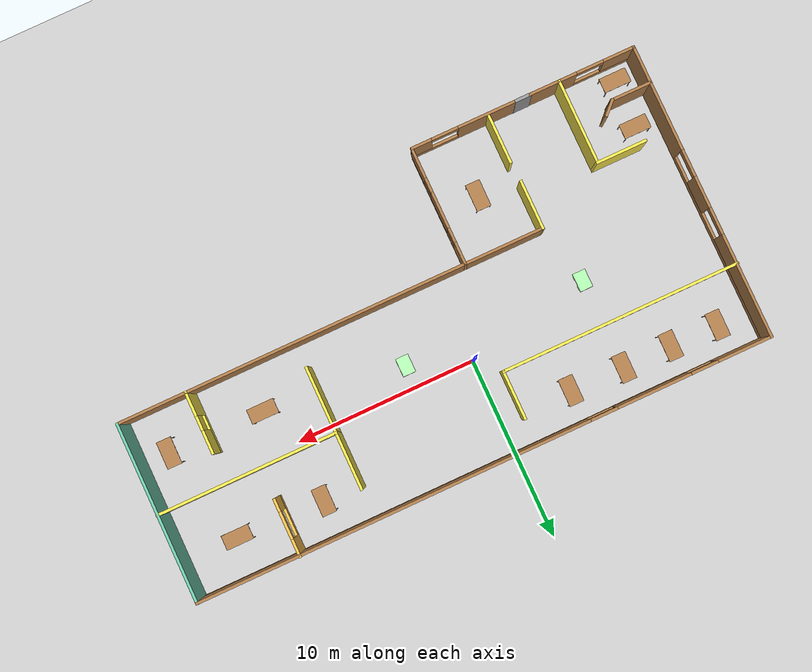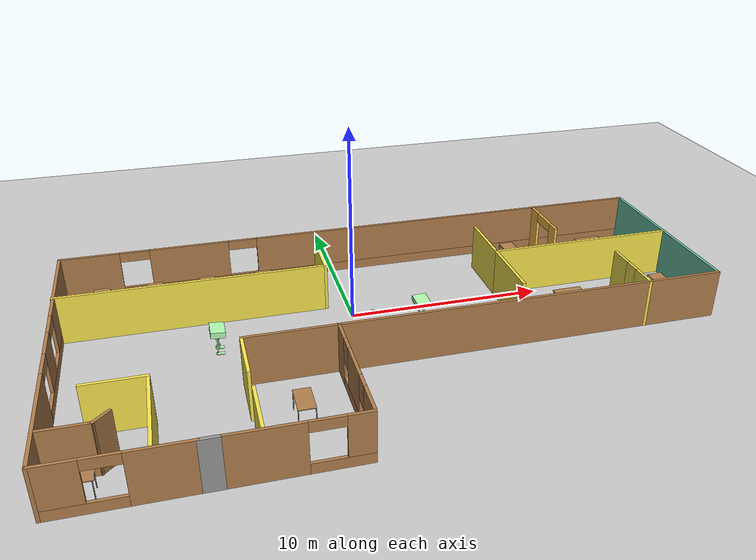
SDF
<sdf version="1.6">
 <world name="default">
  <plugin name="welcome" filename="libwelcome.so"/>
  <light name="sun" type="directional">
   <pose>0 0 10 0 -0 0</pose>
   <diffuse>0.8 0.8 0.8 1</diffuse>
   <specular>0.2 0.2 0.2 1</specular>
   <attenuation>
    <range>1000</range>
    <constant>0.9</constant>
    <linear>0.01</linear>
    <quadratic>0.001</quadratic>
   </attenuation>
   <direction>-0.5 0.1 -0.9</direction>
  </light>
  <model name="ground_plane">
   <static>1</static>
   <link name="link">
    <collision name="collision">
     <geometry><plane><normal>0 0 1</normal><size>100 100</size></plane></geometry>
     <surface>
      <contact><collide_bitmask>65535</collide_bitmask></contact>
      <friction><ode><mu>100</mu><mu2>50</mu2></ode></friction>
     </surface>
    </collision>
    <visual name="visual">
     <cast_shadows>0</cast_shadows>
     <geometry><plane><normal>0 0 1</normal><size>100 100</size></plane></geometry>
     <material>
      <script><uri>file://media/materials/scripts/gazebo.material</uri><name>Gazebo/Grey</name></script>
     </material>
    </visual>
   </link>
  </model>
  <gravity>0 0 -9.8</gravity>
  <magnetic_field>6e-06 2.3e-05 -4.2e-05</magnetic_field>
  <atmosphere type="adiabatic"/>
  <physics name="default_physics" default="0" type="ode">
   <max_step_size>0.001</max_step_size>
   <real_time_factor>1</real_time_factor>
   <real_time_update_rate>1000</real_time_update_rate>
  </physics>
  <scene><ambient>0.4 0.4 0.4 1</ambient><background>0.7 0.7 0.7 1</background><shadows>1</shadows></scene>
  <audio><device>default</device></audio>
  <spherical_coordinates>
   <surface_model>EARTH_WGS84</surface_model>
   <latitude_deg>0</latitude_deg>
   <longitude_deg>0</longitude_deg>
   <elevation>0</elevation>
   <heading_deg>0</heading_deg>
  </spherical_coordinates>
  <model name="Building">
   <pose>1.74375 -2.92955 0 0 -0 0</pose>
   <link name="Door_0">
    <collision name="Door_0_Collision">
     <geometry><box><size>0.9 0.17 2.5</size></box></geometry>
     <pose>0 0 1.25 0 -0 0</pose>
    </collision>
    <visual name="Door_0_Visual">
     <pose>0 0 1.25 0 -0 0</pose>
     <geometry><box><size>0.9 0.17 2.5</size></box></geometry>
     <material>
      <script><uri>file://media/materials/scripts/gazebo.material</uri><name>Gazebo/Grey</name></script>
     </material>
    </visual>
    <pose>-9.65874 -8.18775 0 0 -0 0</pose>
   </link>
   <link name="Wall_1">
    <pose>-12.9888 -8.19111 0 0 -0 3.14159</pose>
    <visual name="Wall_1_Visual_0">
     <pose>-1.645 0 1.25 0 -0 0</pose>
     <geometry><box><size>2.71 0.15 2.5</size></box></geometry>
     <material>
      <script><uri>file://media/materials/scripts/gazebo.material</uri><name>Gazebo/Wood</name></script>
      <ambient>0.435294 0.796078 0.67451 1</ambient>
     </material>
     <meta><layer>0</layer></meta>
    </visual>
    <collision name="Wall_1_Collision_0">
     <geometry><box><size>2.71 0.15 2.5</size></box></geometry>
     <pose>-1.645 0 1.25 0 -0 0</pose>
    </collision>
    <visual name="Wall_1_Visual_1">
     <pose>1.355 0 0.25 0 -0 0</pose>
     <geometry><box><size>3.29 0.15 0.5</size></box></geometry>
     <material>
      <script><uri>file://media/materials/scripts/gazebo.material</uri><name>Gazebo/Wood</name></script>
      <ambient>0.435294 0.796078 0.67451 1</ambient>
     </material>
     <meta><layer>0</layer></meta>
    </visual>
    <collision name="Wall_1_Collision_1">
     <geometry><box><size>3.29 0.15 0.5</size></box></geometry>
     <pose>1.355 0 0.25 0 -0 0</pose>
    </collision>
    <visual name="Wall_1_Visual_2">
     <pose>2.105 0 1.5 0 -0 0</pose>
     <geometry><box><size>1.79 0.15 2</size></box></geometry>
     <material>
      <script><uri>file://media/materials/scripts/gazebo.material</uri><name>Gazebo/Wood</name></script>
      <ambient>0.435294 0.796078 0.67451 1</ambient>
     </material>
     <meta><layer>0</layer></meta>
    </visual>
    <collision name="Wall_1_Collision_2">
     <geometry><box><size>1.79 0.15 2</size></box></geometry>
     <pose>2.105 0 1.5 0 -0 0</pose>
    </collision>
    <visual name="Wall_1_Visual_3">
     <pose>0.46 0 2.25 0 -0 0</pose>
     <geometry><box><size>1.5 0.15 0.5</size></box></geometry>
     <material>
      <script><uri>file://media/materials/scripts/gazebo.material</uri><name>Gazebo/Wood</name></script>
      <ambient>0.435294 0.796078 0.67451 1</ambient>
     </material>
     <meta><layer>0</layer></meta>
    </visual>
    <collision name="Wall_1_Collision_3">
     <geometry><box><size>1.5 0.15 0.5</size></box></geometry>
     <pose>0.46 0 2.25 0 -0 0</pose>
    </collision>
   </link>
   <link name="Wall_11">
    <pose>-15.9138 -0.016115 0 0 -0 1.5708</pose>
    <visual name="Wall_11_Visual_0">
     <pose>-5.28758 0 1.25 0 -0 0</pose>
     <geometry><box><size>5.92484 0.15 2.5</size></box></geometry>
     <material>
      <script><uri>file://media/materials/scripts/gazebo.material</uri><name>Gazebo/Wood</name></script>
      <ambient>0.435294 0.796078 0.67451 1</ambient>
     </material>
     <meta><layer>0</layer></meta>
    </visual>
    <collision name="Wall_11_Collision_0">
     <geometry><box><size>5.92484 0.15 2.5</size></box></geometry>
     <pose>-5.28758 0 1.25 0 -0 0</pose>
    </collision>
    <visual name="Wall_11_Visual_1">
     <pose>2.96242 0 0.25 0 -0 0</pose>
     <geometry><box><size>10.5752 0.15 0.5</size></box></geometry>
     <material>
      <script><uri>file://media/materials/scripts/gazebo.material</uri><name>Gazebo/Wood</name></script>
      <ambient>0.435294 0.796078 0.67451 1</ambient>
     </material>
     <meta><layer>0</layer></meta>
    </visual>
    <collision name="Wall_11_Collision_1">
     <geometry><box><size>10.5752 0.15 0.5</size></box></geometry>
     <pose>2.96242 0 0.25 0 -0 0</pose>
    </collision>
    <visual name="Wall_11_Visual_2">
     <pose>0.058939 0 1.5 0 -0 0</pose>
     <geometry><box><size>1.76821 0.15 2</size></box></geometry>
     <material>
      <script><uri>file://media/materials/scripts/gazebo.material</uri><name>Gazebo/Wood</name></script>
      <ambient>0.435294 0.796078 0.67451 1</ambient>
     </material>
     <meta><layer>0</layer></meta>
    </visual>
    <collision name="Wall_11_Collision_2">
     <geometry><box><size>1.76821 0.15 2</size></box></geometry>
     <pose>0.058939 0 1.5 0 -0 0</pose>
    </collision>
    <visual name="Wall_11_Visual_3">
     <pose>5.34652 0 1.5 0 -0 0</pose>
     <geometry><box><size>5.80696 0.15 2</size></box></geometry>
     <material>
      <script><uri>file://media/materials/scripts/gazebo.material</uri><name>Gazebo/Wood</name></script>
      <ambient>0.435294 0.796078 0.67451 1</ambient>
     </material>
     <meta><layer>0</layer></meta>
    </visual>
    <collision name="Wall_11_Collision_3">
     <geometry><box><size>5.80696 0.15 2</size></box></geometry>
     <pose>5.34652 0 1.5 0 -0 0</pose>
    </collision>
    <visual name="Wall_11_Visual_4">
     <pose>-1.57516 0 2.25 0 -0 0</pose>
     <geometry><box><size>1.5 0.15 0.5</size></box></geometry>
     <material>
      <script><uri>file://media/materials/scripts/gazebo.material</uri><name>Gazebo/Wood</name></script>
      <ambient>0.435294 0.796078 0.67451 1</ambient>
     </material>
     <meta><layer>0</layer></meta>
    </visual>
    <collision name="Wall_11_Collision_4">
     <geometry><box><size>1.5 0.15 0.5</size></box></geometry>
     <pose>-1.57516 0 2.25 0 -0 0</pose>
    </collision>
    <visual name="Wall_11_Visual_5">
     <pose>1.69304 0 2.25 0 -0 0</pose>
     <geometry><box><size>1.5 0.15 0.5</size></box></geometry>
     <material>
      <script><uri>file://media/materials/scripts/gazebo.material</uri><name>Gazebo/Wood</name></script>
      <ambient>0.435294 0.796078 0.67451 1</ambient>
     </material>
     <meta><layer>0</layer></meta>
    </visual>
    <collision name="Wall_11_Collision_5">
     <geometry><box><size>1.5 0.15 0.5</size></box></geometry>
     <pose>1.69304 0 2.25 0 -0 0</pose>
    </collision>
   </link>
   <link name="Wall_12">
    <pose>0.011207 8.15888 0 0 -0 0</pose>
    <visual name="Wall_12_Visual_0">
     <pose>-14.4756 0 1.25 0 -0 0</pose>
     <geometry><box><size>3.04875 0.15 2.5</size></box></geometry>
     <material>
      <script><uri>file://media/materials/scripts/gazebo.material</uri><name>Gazebo/Wood</name></script>
      <ambient>0.435294 0.796078 0.67451 1</ambient>
     </material>
     <meta><layer>0</layer></meta>
    </visual>
    <collision name="Wall_12_Collision_0">
     <geometry><box><size>3.04875 0.15 2.5</size></box></geometry>
     <pose>-14.4756 0 1.25 0 -0 0</pose>
    </collision>
    <visual name="Wall_12_Visual_1">
     <pose>1.52438 0 0.25 0 -0 0</pose>
     <geometry><box><size>28.9513 0.15 0.5</size></box></geometry>
     <material>
      <script><uri>file://media/materials/scripts/gazebo.material</uri><name>Gazebo/Wood</name></script>
      <ambient>0.435294 0.796078 0.67451 1</ambient>
     </material>
     <meta><layer>0</layer></meta>
    </visual>
    <collision name="Wall_12_Collision_1">
     <geometry><box><size>28.9513 0.15 0.5</size></box></geometry>
     <pose>1.52438 0 0.25 0 -0 0</pose>
    </collision>
    <visual name="Wall_12_Visual_2">
     <pose>-9.39504 0 1.5 0 -0 0</pose>
     <geometry><box><size>4.11241 0.15 2</size></box></geometry>
     <material>
      <script><uri>file://media/materials/scripts/gazebo.material</uri><name>Gazebo/Wood</name></script>
      <ambient>0.435294 0.796078 0.67451 1</ambient>
     </material>
     <meta><layer>0</layer></meta>
    </visual>
    <collision name="Wall_12_Collision_2">
     <geometry><box><size>4.11241 0.15 2</size></box></geometry>
     <pose>-9.39504 0 1.5 0 -0 0</pose>
    </collision>
    <visual name="Wall_12_Visual_3">
     <pose>5.08058 0 1.5 0 -0 0</pose>
     <geometry><box><size>21.8388 0.15 2</size></box></geometry>
     <material>
      <script><uri>file://media/materials/scripts/gazebo.material</uri><name>Gazebo/Wood</name></script>
      <ambient>0.435294 0.796078 0.67451 1</ambient>
     </material>
     <meta><layer>0</layer></meta>
    </visual>
    <collision name="Wall_12_Collision_3">
     <geometry><box><size>21.8388 0.15 2</size></box></geometry>
     <pose>5.08058 0 1.5 0 -0 0</pose>
    </collision>
    <visual name="Wall_12_Visual_4">
     <pose>-12.2012 0 2.25 0 -0 0</pose>
     <geometry><box><size>1.5 0.15 0.5</size></box></geometry>
     <material>
      <script><uri>file://media/materials/scripts/gazebo.material</uri><name>Gazebo/Wood</name></script>
      <ambient>0.435294 0.796078 0.67451 1</ambient>
     </material>
     <meta><layer>0</layer></meta>
    </visual>
    <collision name="Wall_12_Collision_4">
     <geometry><box><size>1.5 0.15 0.5</size></box></geometry>
     <pose>-12.2012 0 2.25 0 -0 0</pose>
    </collision>
    <visual name="Wall_12_Visual_5">
     <pose>-6.58884 0 2.25 0 -0 0</pose>
     <geometry><box><size>1.5 0.15 0.5</size></box></geometry>
     <material>
      <script><uri>file://media/materials/scripts/gazebo.material</uri><name>Gazebo/Wood</name></script>
      <ambient>0.435294 0.796078 0.67451 1</ambient>
     </material>
     <meta><layer>0</layer></meta>
    </visual>
    <collision name="Wall_12_Collision_5">
     <geometry><box><size>1.5 0.15 0.5</size></box></geometry>
     <pose>-6.58884 0 2.25 0 -0 0</pose>
    </collision>
   </link>
   <link name="Wall_13">
    <collision name="Wall_13_Collision">
     <geometry><box><size>10 0.15 2.5</size></box></geometry>
     <pose>0 0 1.25 0 -0 0</pose>
    </collision>
    <visual name="Wall_13_Visual">
     <pose>0 0 1.25 0 -0 0</pose>
     <geometry><box><size>10 0.15 2.5</size></box></geometry>
     <material>
      <script><uri>file://media/materials/scripts/gazebo.material</uri><name>Gazebo/Grey</name></script>
      <ambient>0.435294 0.796078 0.67451 1</ambient>
     </material>
     <meta><layer>0</layer></meta>
    </visual>
    <pose>15.9362 3.23388 0 0 -0 -1.5708</pose>
   </link>
   <link name="Wall_14">
    <collision name="Wall_14_Collision">
     <geometry><box><size>19.4856 0.15 2.5</size></box></geometry>
     <pose>0 0 1.25 0 -0 0</pose>
    </collision>
    <visual name="Wall_14_Visual">
     <pose>0 0 1.25 0 -0 0</pose>
     <geometry><box><size>19.4856 0.15 2.5</size></box></geometry>
     <material>
      <script><uri>file://media/materials/scripts/gazebo.material</uri><name>Gazebo/Wood</name></script>
      <ambient>0.435294 0.796078 0.67451 1</ambient>
     </material>
     <meta><layer>0</layer></meta>
    </visual>
    <pose>6.26821 -1.69111 0 0 -0 3.14159</pose>
   </link>
   <link name="Wall_15">
    <pose>-3.39979 -4.87312 0 0 -0 -1.5708</pose>
    <visual name="Wall_15_Visual_0">
     <pose>-2.61589 0 1.25 0 -0 0</pose>
     <geometry><box><size>1.28264 0.15 2.5</size></box></geometry>
     <material>
      <script><uri>file://media/materials/scripts/gazebo.material</uri><name>Gazebo/Wood</name></script>
      <ambient>0.435294 0.796078 0.67451 1</ambient>
     </material>
     <meta><layer>0</layer></meta>
    </visual>
    <collision name="Wall_15_Collision_0">
     <geometry><box><size>1.28264 0.15 2.5</size></box></geometry>
     <pose>-2.61589 0 1.25 0 -0 0</pose>
    </collision>
    <visual name="Wall_15_Visual_1">
     <pose>0.641319 0 0.25 0 -0 0</pose>
     <geometry><box><size>5.23177 0.15 0.5</size></box></geometry>
     <material>
      <script><uri>file://media/materials/scripts/gazebo.material</uri><name>Gazebo/Wood</name></script>
      <ambient>0.435294 0.796078 0.67451 1</ambient>
     </material>
     <meta><layer>0</layer></meta>
    </visual>
    <collision name="Wall_15_Collision_1">
     <geometry><box><size>5.23177 0.15 0.5</size></box></geometry>
     <pose>0.641319 0 0.25 0 -0 0</pose>
    </collision>
    <visual name="Wall_15_Visual_2">
     <pose>-0.15997 0 1.5 0 -0 0</pose>
     <geometry><box><size>2.02919 0.15 2</size></box></geometry>
     <material>
      <script><uri>file://media/materials/scripts/gazebo.material</uri><name>Gazebo/Wood</name></script>
      <ambient>0.435294 0.796078 0.67451 1</ambient>
     </material>
     <meta><layer>0</layer></meta>
    </visual>
    <collision name="Wall_15_Collision_2">
     <geometry><box><size>2.02919 0.15 2</size></box></geometry>
     <pose>-0.15997 0 1.5 0 -0 0</pose>
    </collision>
    <visual name="Wall_15_Visual_3">
     <pose>2.45592 0 1.5 0 -0 0</pose>
     <geometry><box><size>1.60258 0.15 2</size></box></geometry>
     <material>
      <script><uri>file://media/materials/scripts/gazebo.material</uri><name>Gazebo/Wood</name></script>
      <ambient>0.435294 0.796078 0.67451 1</ambient>
     </material>
     <meta><layer>0</layer></meta>
    </visual>
    <collision name="Wall_15_Collision_3">
     <geometry><box><size>1.60258 0.15 2</size></box></geometry>
     <pose>2.45592 0 1.5 0 -0 0</pose>
    </collision>
    <visual name="Wall_15_Visual_4">
     <pose>-1.57457 0 1.9 0 -0 0</pose>
     <geometry><box><size>0.8 0.15 1.2</size></box></geometry>
     <material>
      <script><uri>file://media/materials/scripts/gazebo.material</uri><name>Gazebo/Wood</name></script>
      <ambient>0.435294 0.796078 0.67451 1</ambient>
     </material>
     <meta><layer>0</layer></meta>
    </visual>
    <collision name="Wall_15_Collision_4">
     <geometry><box><size>0.8 0.15 1.2</size></box></geometry>
     <pose>-1.57457 0 1.9 0 -0 0</pose>
    </collision>
    <visual name="Wall_15_Visual_5">
     <pose>1.25463 0 1.9 0 -0 0</pose>
     <geometry><box><size>0.8 0.15 1.2</size></box></geometry>
     <material>
      <script><uri>file://media/materials/scripts/gazebo.material</uri><name>Gazebo/Wood</name></script>
      <ambient>0.435294 0.796078 0.67451 1</ambient>
     </material>
     <meta><layer>0</layer></meta>
    </visual>
    <collision name="Wall_15_Collision_5">
     <geometry><box><size>0.8 0.15 1.2</size></box></geometry>
     <pose>1.25463 0 1.9 0 -0 0</pose>
    </collision>
   </link>
   <link name="Wall_20">
    <collision name="Wall_20_Collision">
     <geometry><box><size>4.5 0.15 2.5</size></box></geometry>
     <pose>0 0 1.25 0 -0 0</pose>
    </collision>
    <visual name="Wall_20_Visual">
     <pose>0 0 1.25 0 -0 0</pose>
     <geometry><box><size>4.5 0.15 2.5</size></box></geometry>
     <material>
      <script><uri>file://media/materials/scripts/gazebo.material</uri><name>Gazebo/Wood</name></script>
      <ambient>0.988235 0.913725 0.309804 1</ambient>
     </material>
     <meta><layer>0</layer></meta>
    </visual>
    <pose>-5.57479 -1.69111 0 0 -0 -3.14159</pose>
   </link>
   <link name="Wall_21">
    <collision name="Wall_21_Collision">
     <geometry><box><size>2.76441 0.15 2.5</size></box></geometry>
     <pose>0 0 1.25 0 -0 0</pose>
    </collision>
    <visual name="Wall_21_Visual">
     <pose>0 0 1.25 0 -0 0</pose>
     <geometry><box><size>2.76441 0.15 2.5</size></box></geometry>
     <material>
      <script><uri>file://media/materials/scripts/gazebo.material</uri><name>Gazebo/Grey</name></script>
      <ambient>0.988235 0.913725 0.309804 1</ambient>
     </material>
     <meta><layer>0</layer></meta>
    </visual>
    <pose>-7.74959 -2.99832 0 0 -0 -1.57064</pose>
   </link>
   <link name="Wall_23">
    <collision name="Wall_23_Collision">
     <geometry><box><size>2.75 0.15 2.5</size></box></geometry>
     <pose>0 0 1.25 0 -0 0</pose>
    </collision>
    <visual name="Wall_23_Visual">
     <pose>0 0 1.25 0 -0 0</pose>
     <geometry><box><size>2.75 0.15 2.5</size></box></geometry>
     <material>
      <script><uri>file://media/materials/scripts/gazebo.material</uri><name>Gazebo/Grey</name></script>
      <ambient>0.988235 0.913725 0.309804 1</ambient>
     </material>
     <meta><layer>0</layer></meta>
    </visual>
    <pose>-7.68166 -6.75545 0 0 -0 -1.5708</pose>
   </link>
   <link name="Wall_27">
    <collision name="Wall_27_Collision">
     <geometry><box><size>10 0.15 2.5</size></box></geometry>
     <pose>0 0 1.25 0 -0 0</pose>
    </collision>
    <visual name="Wall_27_Visual">
     <pose>0 0 1.25 0 -0 0</pose>
     <geometry><box><size>10 0.15 2.5</size></box></geometry>
     <material>
      <script><uri>file://media/materials/scripts/gazebo.material</uri><name>Gazebo/Grey</name></script>
      <ambient>0.988235 0.913725 0.309804 1</ambient>
     </material>
     <meta><layer>0</layer></meta>
    </visual>
    <pose>11.0323 3.33245 0 0 -0 3.14159</pose>
   </link>
   <link name="Wall_28">
    <collision name="Wall_28_Collision">
     <geometry><box><size>3.25 0.15 2.5</size></box></geometry>
     <pose>0 0 1.25 0 -0 0</pose>
    </collision>
    <visual name="Wall_28_Visual">
     <pose>0 0 1.25 0 -0 0</pose>
     <geometry><box><size>3.25 0.15 2.5</size></box></geometry>
     <material>
      <script><uri>file://media/materials/scripts/gazebo.material</uri><name>Gazebo/Grey</name></script>
      <ambient>0.988235 0.913725 0.309804 1</ambient>
     </material>
     <meta><layer>0</layer></meta>
    </visual>
    <pose>6.10728 4.88245 0 0 -0 1.5708</pose>
   </link>
   <link name="Wall_3">
    <pose>-6.29879 -8.19111 0 0 -0 0</pose>
    <visual name="Wall_3_Visual_0">
     <pose>-1.32758 0 1.25 0 -0 0</pose>
     <geometry><box><size>3.24484 0.15 2.5</size></box></geometry>
     <material>
      <script><uri>file://media/materials/scripts/gazebo.material</uri><name>Gazebo/Wood</name></script>
      <ambient>0.435294 0.796078 0.67451 1</ambient>
     </material>
     <meta><layer>0</layer></meta>
    </visual>
    <collision name="Wall_3_Collision_0">
     <geometry><box><size>3.24484 0.15 2.5</size></box></geometry>
     <pose>-1.32758 0 1.25 0 -0 0</pose>
    </collision>
    <visual name="Wall_3_Visual_1">
     <pose>1.62242 0 0.25 0 -0 0</pose>
     <geometry><box><size>2.65516 0.15 0.5</size></box></geometry>
     <material>
      <script><uri>file://media/materials/scripts/gazebo.material</uri><name>Gazebo/Wood</name></script>
      <ambient>0.435294 0.796078 0.67451 1</ambient>
     </material>
     <meta><layer>0</layer></meta>
    </visual>
    <collision name="Wall_3_Collision_1">
     <geometry><box><size>2.65516 0.15 0.5</size></box></geometry>
     <pose>1.62242 0 0.25 0 -0 0</pose>
    </collision>
    <visual name="Wall_3_Visual_2">
     <pose>2.37242 0 1.5 0 -0 0</pose>
     <geometry><box><size>1.15516 0.15 2</size></box></geometry>
     <material>
      <script><uri>file://media/materials/scripts/gazebo.material</uri><name>Gazebo/Wood</name></script>
      <ambient>0.435294 0.796078 0.67451 1</ambient>
     </material>
     <meta><layer>0</layer></meta>
    </visual>
    <collision name="Wall_3_Collision_2">
     <geometry><box><size>1.15516 0.15 2</size></box></geometry>
     <pose>2.37242 0 1.5 0 -0 0</pose>
    </collision>
    <visual name="Wall_3_Visual_3">
     <pose>1.04484 0 2.25 0 -0 0</pose>
     <geometry><box><size>1.5 0.15 0.5</size></box></geometry>
     <material>
      <script><uri>file://media/materials/scripts/gazebo.material</uri><name>Gazebo/Wood</name></script>
      <ambient>0.435294 0.796078 0.67451 1</ambient>
     </material>
     <meta><layer>0</layer></meta>
    </visual>
    <collision name="Wall_3_Collision_3">
     <geometry><box><size>1.5 0.15 0.5</size></box></geometry>
     <pose>1.04484 0 2.25 0 -0 0</pose>
    </collision>
   </link>
   <link name="Wall_30">
    <collision name="Wall_30_Collision">
     <geometry><box><size>3.75 0.15 2.5</size></box></geometry>
     <pose>0 0 1.25 0 -0 0</pose>
    </collision>
    <visual name="Wall_30_Visual">
     <pose>0 0 1.25 0 -0 0</pose>
     <geometry><box><size>3.75 0.15 2.5</size></box></geometry>
     <material>
      <script><uri>file://media/materials/scripts/gazebo.material</uri><name>Gazebo/Grey</name></script>
      <ambient>0.988235 0.913725 0.309804 1</ambient>
     </material>
     <meta><layer>0</layer></meta>
    </visual>
    <pose>6.10728 1.53245 0 0 -0 -1.5708</pose>
   </link>
   <link name="Wall_32">
    <collision name="Wall_32_Collision">
     <geometry><box><size>13.25 0.15 2.5</size></box></geometry>
     <pose>0 0 1.25 0 -0 0</pose>
    </collision>
    <visual name="Wall_32_Visual">
     <pose>0 0 1.25 0 -0 0</pose>
     <geometry><box><size>13.25 0.15 2.5</size></box></geometry>
     <material>
      <script><uri>file://media/materials/scripts/gazebo.material</uri><name>Gazebo/Grey</name></script>
      <ambient>0.988235 0.913725 0.309804 1</ambient>
     </material>
     <meta><layer>0</layer></meta>
    </visual>
    <pose>-9.40728 4.07713 0 0 -0 0</pose>
   </link>
   <link name="Wall_33">
    <collision name="Wall_33_Collision">
     <geometry><box><size>2.75 0.15 2.5</size></box></geometry>
     <pose>0 0 1.25 0 -0 0</pose>
    </collision>
    <visual name="Wall_33_Visual">
     <pose>0 0 1.25 0 -0 0</pose>
     <geometry><box><size>2.75 0.15 2.5</size></box></geometry>
     <material>
      <script><uri>file://media/materials/scripts/gazebo.material</uri><name>Gazebo/Grey</name></script>
      <ambient>0.988235 0.913725 0.309804 1</ambient>
     </material>
     <meta><layer>0</layer></meta>
    </visual>
    <pose>-2.85728 5.37713 0 0 -0 1.5708</pose>
   </link>
   <link name="Wall_37">
    <pose>12.1544 -0.018507 0 0 -0 1.5708</pose>
    <visual name="Wall_37_Visual_0">
     <pose>-1.05653 0 1.25 0 -0 0</pose>
     <geometry><box><size>1.38694 0.15 2.5</size></box></geometry>
     <material>
      <script><uri>file://media/materials/scripts/gazebo.material</uri><name>Gazebo/Grey</name></script>
      <ambient>0.988235 0.913725 0.309804 1</ambient>
     </material>
     <meta><layer>0</layer></meta>
    </visual>
    <collision name="Wall_37_Collision_0">
     <geometry><box><size>1.38694 0.15 2.5</size></box></geometry>
     <pose>-1.05653 0 1.25 0 -0 0</pose>
    </collision>
    <visual name="Wall_37_Visual_1">
     <pose>0.693471 0 0.25 0 -0 0</pose>
     <geometry><box><size>2.11306 0.15 0.5</size></box></geometry>
     <material>
      <script><uri>file://media/materials/scripts/gazebo.material</uri><name>Gazebo/Grey</name></script>
      <ambient>0.988235 0.913725 0.309804 1</ambient>
     </material>
     <meta><layer>0</layer></meta>
    </visual>
    <collision name="Wall_37_Collision_1">
     <geometry><box><size>2.11306 0.15 0.5</size></box></geometry>
     <pose>0.693471 0 0.25 0 -0 0</pose>
    </collision>
    <visual name="Wall_37_Visual_2">
     <pose>1.09347 0 1.5 0 -0 0</pose>
     <geometry><box><size>1.31306 0.15 2</size></box></geometry>
     <material>
      <script><uri>file://media/materials/scripts/gazebo.material</uri><name>Gazebo/Grey</name></script>
      <ambient>0.988235 0.913725 0.309804 1</ambient>
     </material>
     <meta><layer>0</layer></meta>
    </visual>
    <collision name="Wall_37_Collision_2">
     <geometry><box><size>1.31306 0.15 2</size></box></geometry>
     <pose>1.09347 0 1.5 0 -0 0</pose>
    </collision>
    <visual name="Wall_37_Visual_3">
     <pose>0.036942 0 1.9 0 -0 0</pose>
     <geometry><box><size>0.8 0.15 1.2</size></box></geometry>
     <material>
      <script><uri>file://media/materials/scripts/gazebo.material</uri><name>Gazebo/Grey</name></script>
      <ambient>0.988235 0.913725 0.309804 1</ambient>
     </material>
     <meta><layer>0</layer></meta>
    </visual>
    <collision name="Wall_37_Collision_3">
     <geometry><box><size>0.8 0.15 1.2</size></box></geometry>
     <pose>0.036942 0 1.9 0 -0 0</pose>
    </collision>
   </link>
   <link name="Wall_39">
    <collision name="Wall_39_Collision">
     <geometry><box><size>4.75 0.15 2.5</size></box></geometry>
     <pose>0 0 1.25 0 -0 0</pose>
    </collision>
    <visual name="Wall_39_Visual">
     <pose>0 0 1.25 0 -0 0</pose>
     <geometry><box><size>4.75 0.15 2.5</size></box></geometry>
     <material>
      <script><uri>file://media/materials/scripts/gazebo.material</uri><name>Gazebo/Grey</name></script>
      <ambient>0.988235 0.913725 0.309804 1</ambient>
     </material>
     <meta><layer>0</layer></meta>
    </visual>
    <pose>-11.7048 -5.87777 0 0 -0 1.5708</pose>
   </link>
   <link name="Wall_40">
    <collision name="Wall_40_Collision">
     <geometry><box><size>2.84281 0.15 2.5</size></box></geometry>
     <pose>0 0 1.25 0 -0 0</pose>
    </collision>
    <visual name="Wall_40_Visual">
     <pose>0 0 1.25 0 -0 0</pose>
     <geometry><box><size>2.84281 0.15 2.5</size></box></geometry>
     <material>
      <script><uri>file://media/materials/scripts/gazebo.material</uri><name>Gazebo/Grey</name></script>
      <ambient>0.988235 0.913725 0.309804 1</ambient>
     </material>
     <meta><layer>0</layer></meta>
    </visual>
    <pose>-13.0509 -3.56347 0 0 -0 3.14159</pose>
   </link>
   <link name="Wall_42">
    <pose>10.3041 6.64112 0 0 -0 -1.5708</pose>
    <visual name="Wall_42_Visual_0">
     <pose>-1.11989 0 1.25 0 -0 0</pose>
     <geometry><box><size>1.01023 0.15 2.5</size></box></geometry>
     <material>
      <script><uri>file://media/materials/scripts/gazebo.material</uri><name>Gazebo/Grey</name></script>
      <ambient>1 0.764706 0.305882 1</ambient>
     </material>
     <meta><layer>0</layer></meta>
    </visual>
    <collision name="Wall_42_Collision_0">
     <geometry><box><size>1.01023 0.15 2.5</size></box></geometry>
     <pose>-1.11989 0 1.25 0 -0 0</pose>
    </collision>
    <visual name="Wall_42_Visual_1">
     <pose>0.505115 0 0.25 0 -0 0</pose>
     <geometry><box><size>2.23977 0.15 0.5</size></box></geometry>
     <material>
      <script><uri>file://media/materials/scripts/gazebo.material</uri><name>Gazebo/Grey</name></script>
      <ambient>1 0.764706 0.305882 1</ambient>
     </material>
     <meta><layer>0</layer></meta>
    </visual>
    <collision name="Wall_42_Collision_1">
     <geometry><box><size>2.23977 0.15 0.5</size></box></geometry>
     <pose>0.505115 0 0.25 0 -0 0</pose>
    </collision>
    <visual name="Wall_42_Visual_2">
     <pose>1.25511 0 1.5 0 -0 0</pose>
     <geometry><box><size>0.73977 0.15 2</size></box></geometry>
     <material>
      <script><uri>file://media/materials/scripts/gazebo.material</uri><name>Gazebo/Grey</name></script>
      <ambient>1 0.764706 0.305882 1</ambient>
     </material>
     <meta><layer>0</layer></meta>
    </visual>
    <collision name="Wall_42_Collision_2">
     <geometry><box><size>0.73977 0.15 2</size></box></geometry>
     <pose>1.25511 0 1.5 0 -0 0</pose>
    </collision>
    <visual name="Wall_42_Visual_3">
     <pose>0.13523 0 2.25 0 -0 0</pose>
     <geometry><box><size>1.5 0.15 0.5</size></box></geometry>
     <material>
      <script><uri>file://media/materials/scripts/gazebo.material</uri><name>Gazebo/Grey</name></script>
      <ambient>1 0.764706 0.305882 1</ambient>
     </material>
     <meta><layer>0</layer></meta>
    </visual>
    <collision name="Wall_42_Collision_3">
     <geometry><box><size>1.5 0.15 0.5</size></box></geometry>
     <pose>0.13523 0 2.25 0 -0 0</pose>
    </collision>
   </link>
   <link name="Wall_44">
    <collision name="Wall_44_Collision">
     <geometry><box><size>2.25 0.15 2.5</size></box></geometry>
     <pose>0 0 1.25 0 -0 0</pose>
    </collision>
    <visual name="Wall_44_Visual">
     <pose>0 0 1.25 0 -0 0</pose>
     <geometry><box><size>2.25 0.15 2.5</size></box></geometry>
     <material>
      <script><uri>file://media/materials/scripts/gazebo.material</uri><name>Gazebo/Wood</name></script>
      <ambient>1 1 1 1</ambient>
     </material>
     <meta><layer>0</layer></meta>
    </visual>
    <pose>-14.8157 -6.17006 0 0 -0 0</pose>
   </link>
   <link name="Wall_45">
    <collision name="Wall_45_Collision">
     <geometry><box><size>1 0.15 2.5</size></box></geometry>
     <pose>0 0 1.25 0 -0 0</pose>
    </collision>
    <visual name="Wall_45_Visual">
     <pose>0 0 1.25 0 -0 0</pose>
     <geometry><box><size>1 0.15 2.5</size></box></geometry>
     <material>
      <script><uri>file://media/materials/scripts/gazebo.material</uri><name>Gazebo/Wood</name></script>
      <ambient>1 1 1 1</ambient>
     </material>
     <meta><layer>0</layer></meta>
    </visual>
    <pose>-13.4652 -5.86954 0 0 -0 0.785398</pose>
   </link>
   <static>1</static>
  </model>
  <model name="table">
   <static>1</static>
   <link name="link">
    <collision name="surface">
     <pose>0 0 1 0 -0 0</pose>
     <geometry><box><size>1.5 0.8 0.03</size></box></geometry>
     <surface><friction><ode><mu>0.6</mu><mu2>0.6</mu2></ode></friction></surface>
    </collision>
    <visual name="visual1">
     <pose>0 0 1 0 -0 0</pose>
     <geometry><box><size>1.5 0.8 0.03</size></box></geometry>
     <material>
      <script><uri>file://media/materials/scripts/gazebo.material</uri><name>Gazebo/Wood</name></script>
     </material>
    </visual>
    <collision name="front_left_leg">
     <pose>0.68 0.38 0.5 0 -0 0</pose>
     <geometry><cylinder><radius>0.02</radius><length>1</length></cylinder></geometry>
    </collision>
    <visual name="front_left_leg">
     <pose>0.68 0.38 0.5 0 -0 0</pose>
     <geometry><cylinder><radius>0.02</radius><length>1</length></cylinder></geometry>
     <material>
      <script><uri>file://media/materials/scripts/gazebo.material</uri><name>Gazebo/Grey</name></script>
     </material>
    </visual>
    <collision name="front_right_leg">
     <pose>0.68 -0.38 0.5 0 -0 0</pose>
     <geometry><cylinder><radius>0.02</radius><length>1</length></cylinder></geometry>
    </collision>
    <visual name="front_right_leg">
     <pose>0.68 -0.38 0.5 0 -0 0</pose>
     <geometry><cylinder><radius>0.02</radius><length>1</length></cylinder></geometry>
     <material>
      <script><uri>file://media/materials/scripts/gazebo.material</uri><name>Gazebo/Grey</name></script>
     </material>
    </visual>
    <collision name="back_right_leg">
     <pose>-0.68 -0.38 0.5 0 -0 0</pose>
     <geometry><cylinder><radius>0.02</radius><length>1</length></cylinder></geometry>
    </collision>
    <visual name="back_right_leg">
     <pose>-0.68 -0.38 0.5 0 -0 0</pose>
     <geometry><cylinder><radius>0.02</radius><length>1</length></cylinder></geometry>
     <material>
      <script><uri>file://media/materials/scripts/gazebo.material</uri><name>Gazebo/Grey</name></script>
     </material>
    </visual>
    <collision name="back_left_leg">
     <pose>-0.68 0.38 0.5 0 -0 0</pose>
     <geometry><cylinder><radius>0.02</radius><length>1</length></cylinder></geometry>
    </collision>
    <visual name="back_left_leg">
     <pose>-0.68 0.38 0.5 0 -0 0</pose>
     <geometry><cylinder><radius>0.02</radius><length>1</length></cylinder></geometry>
     <material>
      <script><uri>file://media/materials/scripts/gazebo.material</uri><name>Gazebo/Grey</name></script>
     </material>
    </visual>
   </link>
   <pose>-3.84994 -7.70139 0 0 0 -1.57545</pose>
  </model>
  <model name="table_0">
   <static>1</static>
   <link name="link">
    <collision name="surface">
     <pose>0 0 1 0 -0 0</pose>
     <geometry><box><size>1.5 0.8 0.03</size></box></geometry>
     <surface><friction><ode><mu>0.6</mu><mu2>0.6</mu2></ode></friction></surface>
    </collision>
    <visual name="visual1">
     <pose>0 0 1 0 -0 0</pose>
     <geometry><box><size>1.5 0.8 0.03</size></box></geometry>
     <material>
      <script><uri>file://media/materials/scripts/gazebo.material</uri><name>Gazebo/Wood</name></script>
     </material>
    </visual>
    <collision name="front_left_leg">
     <pose>0.68 0.38 0.5 0 -0 0</pose>
     <geometry><cylinder><radius>0.02</radius><length>1</length></cylinder></geometry>
    </collision>
    <visual name="front_left_leg">
     <pose>0.68 0.38 0.5 0 -0 0</pose>
     <geometry><cylinder><radius>0.02</radius><length>1</length></cylinder></geometry>
     <material>
      <script><uri>file://media/materials/scripts/gazebo.material</uri><name>Gazebo/Grey</name></script>
     </material>
    </visual>
    <collision name="front_right_leg">
     <pose>0.68 -0.38 0.5 0 -0 0</pose>
     <geometry><cylinder><radius>0.02</radius><length>1</length></cylinder></geometry>
    </collision>
    <visual name="front_right_leg">
     <pose>0.68 -0.38 0.5 0 -0 0</pose>
     <geometry><cylinder><radius>0.02</radius><length>1</length></cylinder></geometry>
     <material>
      <script><uri>file://media/materials/scripts/gazebo.material</uri><name>Gazebo/Grey</name></script>
     </material>
    </visual>
    <collision name="back_right_leg">
     <pose>-0.68 -0.38 0.5 0 -0 0</pose>
     <geometry><cylinder><radius>0.02</radius><length>1</length></cylinder></geometry>
    </collision>
    <visual name="back_right_leg">
     <pose>-0.68 -0.38 0.5 0 -0 0</pose>
     <geometry><cylinder><radius>0.02</radius><length>1</length></cylinder></geometry>
     <material>
      <script><uri>file://media/materials/scripts/gazebo.material</uri><name>Gazebo/Grey</name></script>
     </material>
    </visual>
    <collision name="back_left_leg">
     <pose>-0.68 0.38 0.5 0 -0 0</pose>
     <geometry><cylinder><radius>0.02</radius><length>1</length></cylinder></geometry>
    </collision>
    <visual name="back_left_leg">
     <pose>-0.68 0.38 0.5 0 -0 0</pose>
     <geometry><cylinder><radius>0.02</radius><length>1</length></cylinder></geometry>
     <material>
      <script><uri>file://media/materials/scripts/gazebo.material</uri><name>Gazebo/Grey</name></script>
     </material>
    </visual>
   </link>
   <pose>-12.8056 -7.57202 0 0 -0 0</pose>
  </model>
  <model name="table_1">
   <static>1</static>
   <link name="link">
    <collision name="surface">
     <pose>0 0 1 0 -0 0</pose>
     <geometry><box><size>1.5 0.8 0.03</size></box></geometry>
     <surface><friction><ode><mu>0.6</mu><mu2>0.6</mu2></ode></friction></surface>
    </collision>
    <visual name="visual1">
     <pose>0 0 1 0 -0 0</pose>
     <geometry><box><size>1.5 0.8 0.03</size></box></geometry>
     <material>
      <script><uri>file://media/materials/scripts/gazebo.material</uri><name>Gazebo/Wood</name></script>
     </material>
    </visual>
    <collision name="front_left_leg">
     <pose>0.68 0.38 0.5 0 -0 0</pose>
     <geometry><cylinder><radius>0.02</radius><length>1</length></cylinder></geometry>
    </collision>
    <visual name="front_left_leg">
     <pose>0.68 0.38 0.5 0 -0 0</pose>
     <geometry><cylinder><radius>0.02</radius><length>1</length></cylinder></geometry>
     <material>
      <script><uri>file://media/materials/scripts/gazebo.material</uri><name>Gazebo/Grey</name></script>
     </material>
    </visual>
    <collision name="front_right_leg">
     <pose>0.68 -0.38 0.5 0 -0 0</pose>
     <geometry><cylinder><radius>0.02</radius><length>1</length></cylinder></geometry>
    </collision>
    <visual name="front_right_leg">
     <pose>0.68 -0.38 0.5 0 -0 0</pose>
     <geometry><cylinder><radius>0.02</radius><length>1</length></cylinder></geometry>
     <material>
      <script><uri>file://media/materials/scripts/gazebo.material</uri><name>Gazebo/Grey</name></script>
     </material>
    </visual>
    <collision name="back_right_leg">
     <pose>-0.68 -0.38 0.5 0 -0 0</pose>
     <geometry><cylinder><radius>0.02</radius><length>1</length></cylinder></geometry>
    </collision>
    <visual name="back_right_leg">
     <pose>-0.68 -0.38 0.5 0 -0 0</pose>
     <geometry><cylinder><radius>0.02</radius><length>1</length></cylinder></geometry>
     <material>
      <script><uri>file://media/materials/scripts/gazebo.material</uri><name>Gazebo/Grey</name></script>
     </material>
    </visual>
    <collision name="back_left_leg">
     <pose>-0.68 0.38 0.5 0 -0 0</pose>
     <geometry><cylinder><radius>0.02</radius><length>1</length></cylinder></geometry>
    </collision>
    <visual name="back_left_leg">
     <pose>-0.68 0.38 0.5 0 -0 0</pose>
     <geometry><cylinder><radius>0.02</radius><length>1</length></cylinder></geometry>
     <material>
      <script><uri>file://media/materials/scripts/gazebo.material</uri><name>Gazebo/Grey</name></script>
     </material>
    </visual>
   </link>
   <pose>-12.8865 -10.2052 0 0 -0 0</pose>
  </model>
  <model name="table_clone">
   <static>1</static>
   <link name="link">
    <collision name="surface">
     <pose>0 0 1 0 -0 0</pose>
     <geometry><box><size>1.5 0.8 0.03</size></box></geometry>
     <surface><friction><ode><mu>0.6</mu><mu2>0.6</mu2></ode></friction></surface>
    </collision>
    <visual name="visual1">
     <pose>0 0 1 0 -0 0</pose>
     <geometry><box><size>1.5 0.8 0.03</size></box></geometry>
     <material>
      <script><uri>file://media/materials/scripts/gazebo.material</uri><name>Gazebo/Wood</name></script>
     </material>
    </visual>
    <collision name="front_left_leg">
     <pose>0.68 0.38 0.5 0 -0 0</pose>
     <geometry><cylinder><radius>0.02</radius><length>1</length></cylinder></geometry>
    </collision>
    <visual name="front_left_leg">
     <pose>0.68 0.38 0.5 0 -0 0</pose>
     <geometry><cylinder><radius>0.02</radius><length>1</length></cylinder></geometry>
     <material>
      <script><uri>file://media/materials/scripts/gazebo.material</uri><name>Gazebo/Grey</name></script>
     </material>
    </visual>
    <collision name="front_right_leg">
     <pose>0.68 -0.38 0.5 0 -0 0</pose>
     <geometry><cylinder><radius>0.02</radius><length>1</length></cylinder></geometry>
    </collision>
    <visual name="front_right_leg">
     <pose>0.68 -0.38 0.5 0 -0 0</pose>
     <geometry><cylinder><radius>0.02</radius><length>1</length></cylinder></geometry>
     <material>
      <script><uri>file://media/materials/scripts/gazebo.material</uri><name>Gazebo/Grey</name></script>
     </material>
    </visual>
    <collision name="back_right_leg">
     <pose>-0.68 -0.38 0.5 0 -0 0</pose>
     <geometry><cylinder><radius>0.02</radius><length>1</length></cylinder></geometry>
    </collision>
    <visual name="back_right_leg">
     <pose>-0.68 -0.38 0.5 0 -0 0</pose>
     <geometry><cylinder><radius>0.02</radius><length>1</length></cylinder></geometry>
     <material>
      <script><uri>file://media/materials/scripts/gazebo.material</uri><name>Gazebo/Grey</name></script>
     </material>
    </visual>
    <collision name="back_left_leg">
     <pose>-0.68 0.38 0.5 0 -0 0</pose>
     <geometry><cylinder><radius>0.02</radius><length>1</length></cylinder></geometry>
    </collision>
    <visual name="back_left_leg">
     <pose>-0.68 0.38 0.5 0 -0 0</pose>
     <geometry><cylinder><radius>0.02</radius><length>1</length></cylinder></geometry>
     <material>
      <script><uri>file://media/materials/scripts/gazebo.material</uri><name>Gazebo/Grey</name></script>
     </material>
    </visual>
   </link>
   <pose>-3.93387 3.48733 0 0 0 -1.57545</pose>
  </model>
  <model name="table_clone_0">
   <static>1</static>
   <link name="link">
    <collision name="surface">
     <pose>0 0 1 0 -0 0</pose>
     <geometry><box><size>1.5 0.8 0.03</size></box></geometry>
     <surface><friction><ode><mu>0.6</mu><mu2>0.6</mu2></ode></friction></surface>
    </collision>
    <visual name="visual1">
     <pose>0 0 1 0 -0 0</pose>
     <geometry><box><size>1.5 0.8 0.03</size></box></geometry>
     <material>
      <script><uri>file://media/materials/scripts/gazebo.material</uri><name>Gazebo/Wood</name></script>
     </material>
    </visual>
    <collision name="front_left_leg">
     <pose>0.68 0.38 0.5 0 -0 0</pose>
     <geometry><cylinder><radius>0.02</radius><length>1</length></cylinder></geometry>
    </collision>
    <visual name="front_left_leg">
     <pose>0.68 0.38 0.5 0 -0 0</pose>
     <geometry><cylinder><radius>0.02</radius><length>1</length></cylinder></geometry>
     <material>
      <script><uri>file://media/materials/scripts/gazebo.material</uri><name>Gazebo/Grey</name></script>
     </material>
    </visual>
    <collision name="front_right_leg">
     <pose>0.68 -0.38 0.5 0 -0 0</pose>
     <geometry><cylinder><radius>0.02</radius><length>1</length></cylinder></geometry>
    </collision>
    <visual name="front_right_leg">
     <pose>0.68 -0.38 0.5 0 -0 0</pose>
     <geometry><cylinder><radius>0.02</radius><length>1</length></cylinder></geometry>
     <material>
      <script><uri>file://media/materials/scripts/gazebo.material</uri><name>Gazebo/Grey</name></script>
     </material>
    </visual>
    <collision name="back_right_leg">
     <pose>-0.68 -0.38 0.5 0 -0 0</pose>
     <geometry><cylinder><radius>0.02</radius><length>1</length></cylinder></geometry>
    </collision>
    <visual name="back_right_leg">
     <pose>-0.68 -0.38 0.5 0 -0 0</pose>
     <geometry><cylinder><radius>0.02</radius><length>1</length></cylinder></geometry>
     <material>
      <script><uri>file://media/materials/scripts/gazebo.material</uri><name>Gazebo/Grey</name></script>
     </material>
    </visual>
    <collision name="back_left_leg">
     <pose>-0.68 0.38 0.5 0 -0 0</pose>
     <geometry><cylinder><radius>0.02</radius><length>1</length></cylinder></geometry>
    </collision>
    <visual name="back_left_leg">
     <pose>-0.68 0.38 0.5 0 -0 0</pose>
     <geometry><cylinder><radius>0.02</radius><length>1</length></cylinder></geometry>
     <material>
      <script><uri>file://media/materials/scripts/gazebo.material</uri><name>Gazebo/Grey</name></script>
     </material>
    </visual>
   </link>
   <pose>-6.92257 3.55811 0 0 0 -1.57545</pose>
  </model>
  <model name="table_clone_1">
   <static>1</static>
   <link name="link">
    <collision name="surface">
     <pose>0 0 1 0 -0 0</pose>
     <geometry><box><size>1.5 0.8 0.03</size></box></geometry>
     <surface><friction><ode><mu>0.6</mu><mu2>0.6</mu2></ode></friction></surface>
    </collision>
    <visual name="visual1">
     <pose>0 0 1 0 -0 0</pose>
     <geometry><box><size>1.5 0.8 0.03</size></box></geometry>
     <material>
      <script><uri>file://media/materials/scripts/gazebo.material</uri><name>Gazebo/Wood</name></script>
     </material>
    </visual>
    <collision name="front_left_leg">
     <pose>0.68 0.38 0.5 0 -0 0</pose>
     <geometry><cylinder><radius>0.02</radius><length>1</length></cylinder></geometry>
    </collision>
    <visual name="front_left_leg">
     <pose>0.68 0.38 0.5 0 -0 0</pose>
     <geometry><cylinder><radius>0.02</radius><length>1</length></cylinder></geometry>
     <material>
      <script><uri>file://media/materials/scripts/gazebo.material</uri><name>Gazebo/Grey</name></script>
     </material>
    </visual>
    <collision name="front_right_leg">
     <pose>0.68 -0.38 0.5 0 -0 0</pose>
     <geometry><cylinder><radius>0.02</radius><length>1</length></cylinder></geometry>
    </collision>
    <visual name="front_right_leg">
     <pose>0.68 -0.38 0.5 0 -0 0</pose>
     <geometry><cylinder><radius>0.02</radius><length>1</length></cylinder></geometry>
     <material>
      <script><uri>file://media/materials/scripts/gazebo.material</uri><name>Gazebo/Grey</name></script>
     </material>
    </visual>
    <collision name="back_right_leg">
     <pose>-0.68 -0.38 0.5 0 -0 0</pose>
     <geometry><cylinder><radius>0.02</radius><length>1</length></cylinder></geometry>
    </collision>
    <visual name="back_right_leg">
     <pose>-0.68 -0.38 0.5 0 -0 0</pose>
     <geometry><cylinder><radius>0.02</radius><length>1</length></cylinder></geometry>
     <material>
      <script><uri>file://media/materials/scripts/gazebo.material</uri><name>Gazebo/Grey</name></script>
     </material>
    </visual>
    <collision name="back_left_leg">
     <pose>-0.68 0.38 0.5 0 -0 0</pose>
     <geometry><cylinder><radius>0.02</radius><length>1</length></cylinder></geometry>
    </collision>
    <visual name="back_left_leg">
     <pose>-0.68 0.38 0.5 0 -0 0</pose>
     <geometry><cylinder><radius>0.02</radius><length>1</length></cylinder></geometry>
     <material>
      <script><uri>file://media/materials/scripts/gazebo.material</uri><name>Gazebo/Grey</name></script>
     </material>
    </visual>
   </link>
   <pose>-9.59622 3.55811 0 0 0 -1.57545</pose>
  </model>
  <model name="table_clone_2">
   <static>1</static>
   <link name="link">
    <collision name="surface">
     <pose>0 0 1 0 -0 0</pose>
     <geometry><box><size>1.5 0.8 0.03</size></box></geometry>
     <surface><friction><ode><mu>0.6</mu><mu2>0.6</mu2></ode></friction></surface>
    </collision>
    <visual name="visual1">
     <pose>0 0 1 0 -0 0</pose>
     <geometry><box><size>1.5 0.8 0.03</size></box></geometry>
     <material>
      <script><uri>file://media/materials/scripts/gazebo.material</uri><name>Gazebo/Wood</name></script>
     </material>
    </visual>
    <collision name="front_left_leg">
     <pose>0.68 0.38 0.5 0 -0 0</pose>
     <geometry><cylinder><radius>0.02</radius><length>1</length></cylinder></geometry>
    </collision>
    <visual name="front_left_leg">
     <pose>0.68 0.38 0.5 0 -0 0</pose>
     <geometry><cylinder><radius>0.02</radius><length>1</length></cylinder></geometry>
     <material>
      <script><uri>file://media/materials/scripts/gazebo.material</uri><name>Gazebo/Grey</name></script>
     </material>
    </visual>
    <collision name="front_right_leg">
     <pose>0.68 -0.38 0.5 0 -0 0</pose>
     <geometry><cylinder><radius>0.02</radius><length>1</length></cylinder></geometry>
    </collision>
    <visual name="front_right_leg">
     <pose>0.68 -0.38 0.5 0 -0 0</pose>
     <geometry><cylinder><radius>0.02</radius><length>1</length></cylinder></geometry>
     <material>
      <script><uri>file://media/materials/scripts/gazebo.material</uri><name>Gazebo/Grey</name></script>
     </material>
    </visual>
    <collision name="back_right_leg">
     <pose>-0.68 -0.38 0.5 0 -0 0</pose>
     <geometry><cylinder><radius>0.02</radius><length>1</length></cylinder></geometry>
    </collision>
    <visual name="back_right_leg">
     <pose>-0.68 -0.38 0.5 0 -0 0</pose>
     <geometry><cylinder><radius>0.02</radius><length>1</length></cylinder></geometry>
     <material>
      <script><uri>file://media/materials/scripts/gazebo.material</uri><name>Gazebo/Grey</name></script>
     </material>
    </visual>
    <collision name="back_left_leg">
     <pose>-0.68 0.38 0.5 0 -0 0</pose>
     <geometry><cylinder><radius>0.02</radius><length>1</length></cylinder></geometry>
    </collision>
    <visual name="back_left_leg">
     <pose>-0.68 0.38 0.5 0 -0 0</pose>
     <geometry><cylinder><radius>0.02</radius><length>1</length></cylinder></geometry>
     <material>
      <script><uri>file://media/materials/scripts/gazebo.material</uri><name>Gazebo/Grey</name></script>
     </material>
    </visual>
   </link>
   <pose>-12.2499 3.59862 0 0 0 -1.57545</pose>
  </model>
  <model name="table_2">
   <static>1</static>
   <link name="link">
    <collision name="surface">
     <pose>0 0 1 0 -0 0</pose>
     <geometry><box><size>1.5 0.8 0.03</size></box></geometry>
     <surface><friction><ode><mu>0.6</mu><mu2>0.6</mu2></ode></friction></surface>
    </collision>
    <visual name="visual1">
     <pose>0 0 1 0 -0 0</pose>
     <geometry><box><size>1.5 0.8 0.03</size></box></geometry>
     <material>
      <script><uri>file://media/materials/scripts/gazebo.material</uri><name>Gazebo/Wood</name></script>
     </material>
    </visual>
    <collision name="front_left_leg">
     <pose>0.68 0.38 0.5 0 -0 0</pose>
     <geometry><cylinder><radius>0.02</radius><length>1</length></cylinder></geometry>
    </collision>
    <visual name="front_left_leg">
     <pose>0.68 0.38 0.5 0 -0 0</pose>
     <geometry><cylinder><radius>0.02</radius><length>1</length></cylinder></geometry>
     <material>
      <script><uri>file://media/materials/scripts/gazebo.material</uri><name>Gazebo/Grey</name></script>
     </material>
    </visual>
    <collision name="front_right_leg">
     <pose>0.68 -0.38 0.5 0 -0 0</pose>
     <geometry><cylinder><radius>0.02</radius><length>1</length></cylinder></geometry>
    </collision>
    <visual name="front_right_leg">
     <pose>0.68 -0.38 0.5 0 -0 0</pose>
     <geometry><cylinder><radius>0.02</radius><length>1</length></cylinder></geometry>
     <material>
      <script><uri>file://media/materials/scripts/gazebo.material</uri><name>Gazebo/Grey</name></script>
     </material>
    </visual>
    <collision name="back_right_leg">
     <pose>-0.68 -0.38 0.5 0 -0 0</pose>
     <geometry><cylinder><radius>0.02</radius><length>1</length></cylinder></geometry>
    </collision>
    <visual name="back_right_leg">
     <pose>-0.68 -0.38 0.5 0 -0 0</pose>
     <geometry><cylinder><radius>0.02</radius><length>1</length></cylinder></geometry>
     <material>
      <script><uri>file://media/materials/scripts/gazebo.material</uri><name>Gazebo/Grey</name></script>
     </material>
    </visual>
    <collision name="back_left_leg">
     <pose>-0.68 0.38 0.5 0 -0 0</pose>
     <geometry><cylinder><radius>0.02</radius><length>1</length></cylinder></geometry>
    </collision>
    <visual name="back_left_leg">
     <pose>-0.68 0.38 0.5 0 -0 0</pose>
     <geometry><cylinder><radius>0.02</radius><length>1</length></cylinder></geometry>
     <material>
      <script><uri>file://media/materials/scripts/gazebo.material</uri><name>Gazebo/Grey</name></script>
     </material>
    </visual>
   </link>
   <pose>10.9334 -2.20612 0 0 -0 0</pose>
  </model>
  <model name="table_3">
   <static>1</static>
   <link name="link">
    <collision name="surface">
     <pose>0 0 1 0 -0 0</pose>
     <geometry><box><size>1.5 0.8 0.03</size></box></geometry>
     <surface><friction><ode><mu>0.6</mu><mu2>0.6</mu2></ode></friction></surface>
    </collision>
    <visual name="visual1">
     <pose>0 0 1 0 -0 0</pose>
     <geometry><box><size>1.5 0.8 0.03</size></box></geometry>
     <material>
      <script><uri>file://media/materials/scripts/gazebo.material</uri><name>Gazebo/Wood</name></script>
     </material>
    </visual>
    <collision name="front_left_leg">
     <pose>0.68 0.38 0.5 0 -0 0</pose>
     <geometry><cylinder><radius>0.02</radius><length>1</length></cylinder></geometry>
    </collision>
    <visual name="front_left_leg">
     <pose>0.68 0.38 0.5 0 -0 0</pose>
     <geometry><cylinder><radius>0.02</radius><length>1</length></cylinder></geometry>
     <material>
      <script><uri>file://media/materials/scripts/gazebo.material</uri><name>Gazebo/Grey</name></script>
     </material>
    </visual>
    <collision name="front_right_leg">
     <pose>0.68 -0.38 0.5 0 -0 0</pose>
     <geometry><cylinder><radius>0.02</radius><length>1</length></cylinder></geometry>
    </collision>
    <visual name="front_right_leg">
     <pose>0.68 -0.38 0.5 0 -0 0</pose>
     <geometry><cylinder><radius>0.02</radius><length>1</length></cylinder></geometry>
     <material>
      <script><uri>file://media/materials/scripts/gazebo.material</uri><name>Gazebo/Grey</name></script>
     </material>
    </visual>
    <collision name="back_right_leg">
     <pose>-0.68 -0.38 0.5 0 -0 0</pose>
     <geometry><cylinder><radius>0.02</radius><length>1</length></cylinder></geometry>
    </collision>
    <visual name="back_right_leg">
     <pose>-0.68 -0.38 0.5 0 -0 0</pose>
     <geometry><cylinder><radius>0.02</radius><length>1</length></cylinder></geometry>
     <material>
      <script><uri>file://media/materials/scripts/gazebo.material</uri><name>Gazebo/Grey</name></script>
     </material>
    </visual>
    <collision name="back_left_leg">
     <pose>-0.68 0.38 0.5 0 -0 0</pose>
     <geometry><cylinder><radius>0.02</radius><length>1</length></cylinder></geometry>
    </collision>
    <visual name="back_left_leg">
     <pose>-0.68 0.38 0.5 0 -0 0</pose>
     <geometry><cylinder><radius>0.02</radius><length>1</length></cylinder></geometry>
     <material>
      <script><uri>file://media/materials/scripts/gazebo.material</uri><name>Gazebo/Grey</name></script>
     </material>
    </visual>
   </link>
   <pose>14.7616 3.11764 0 0 -0 0</pose>
  </model>
  <model name="table_clone_3">
   <static>1</static>
   <link name="link">
    <collision name="surface">
     <pose>0 0 1 0 -0 0</pose>
     <geometry><box><size>1.5 0.8 0.03</size></box></geometry>
     <surface><friction><ode><mu>0.6</mu><mu2>0.6</mu2></ode></friction></surface>
    </collision>
    <visual name="visual1">
     <pose>0 0 1 0 -0 0</pose>
     <geometry><box><size>1.5 0.8 0.03</size></box></geometry>
     <material>
      <script><uri>file://media/materials/scripts/gazebo.material</uri><name>Gazebo/Wood</name></script>
     </material>
    </visual>
    <collision name="front_left_leg">
     <pose>0.68 0.38 0.5 0 -0 0</pose>
     <geometry><cylinder><radius>0.02</radius><length>1</length></cylinder></geometry>
    </collision>
    <visual name="front_left_leg">
     <pose>0.68 0.38 0.5 0 -0 0</pose>
     <geometry><cylinder><radius>0.02</radius><length>1</length></cylinder></geometry>
     <material>
      <script><uri>file://media/materials/scripts/gazebo.material</uri><name>Gazebo/Grey</name></script>
     </material>
    </visual>
    <collision name="front_right_leg">
     <pose>0.68 -0.38 0.5 0 -0 0</pose>
     <geometry><cylinder><radius>0.02</radius><length>1</length></cylinder></geometry>
    </collision>
    <visual name="front_right_leg">
     <pose>0.68 -0.38 0.5 0 -0 0</pose>
     <geometry><cylinder><radius>0.02</radius><length>1</length></cylinder></geometry>
     <material>
      <script><uri>file://media/materials/scripts/gazebo.material</uri><name>Gazebo/Grey</name></script>
     </material>
    </visual>
    <collision name="back_right_leg">
     <pose>-0.68 -0.38 0.5 0 -0 0</pose>
     <geometry><cylinder><radius>0.02</radius><length>1</length></cylinder></geometry>
    </collision>
    <visual name="back_right_leg">
     <pose>-0.68 -0.38 0.5 0 -0 0</pose>
     <geometry><cylinder><radius>0.02</radius><length>1</length></cylinder></geometry>
     <material>
      <script><uri>file://media/materials/scripts/gazebo.material</uri><name>Gazebo/Grey</name></script>
     </material>
    </visual>
    <collision name="back_left_leg">
     <pose>-0.68 0.38 0.5 0 -0 0</pose>
     <geometry><cylinder><radius>0.02</radius><length>1</length></cylinder></geometry>
    </collision>
    <visual name="back_left_leg">
     <pose>-0.68 0.38 0.5 0 -0 0</pose>
     <geometry><cylinder><radius>0.02</radius><length>1</length></cylinder></geometry>
     <material>
      <script><uri>file://media/materials/scripts/gazebo.material</uri><name>Gazebo/Grey</name></script>
     </material>
    </visual>
   </link>
   <pose>16.1844 -2.27163 0 0 0 -1.57545</pose>
  </model>
  <model name="table_clone_4">
   <static>1</static>
   <link name="link">
    <collision name="surface">
     <pose>0 0 1 0 -0 0</pose>
     <geometry><box><size>1.5 0.8 0.03</size></box></geometry>
     <surface><friction><ode><mu>0.6</mu><mu2>0.6</mu2></ode></friction></surface>
    </collision>
    <visual name="visual1">
     <pose>0 0 1 0 -0 0</pose>
     <geometry><box><size>1.5 0.8 0.03</size></box></geometry>
     <material>
      <script><uri>file://media/materials/scripts/gazebo.material</uri><name>Gazebo/Wood</name></script>
     </material>
    </visual>
    <collision name="front_left_leg">
     <pose>0.68 0.38 0.5 0 -0 0</pose>
     <geometry><cylinder><radius>0.02</radius><length>1</length></cylinder></geometry>
    </collision>
    <visual name="front_left_leg">
     <pose>0.68 0.38 0.5 0 -0 0</pose>
     <geometry><cylinder><radius>0.02</radius><length>1</length></cylinder></geometry>
     <material>
      <script><uri>file://media/materials/scripts/gazebo.material</uri><name>Gazebo/Grey</name></script>
     </material>
    </visual>
    <collision name="front_right_leg">
     <pose>0.68 -0.38 0.5 0 -0 0</pose>
     <geometry><cylinder><radius>0.02</radius><length>1</length></cylinder></geometry>
    </collision>
    <visual name="front_right_leg">
     <pose>0.68 -0.38 0.5 0 -0 0</pose>
     <geometry><cylinder><radius>0.02</radius><length>1</length></cylinder></geometry>
     <material>
      <script><uri>file://media/materials/scripts/gazebo.material</uri><name>Gazebo/Grey</name></script>
     </material>
    </visual>
    <collision name="back_right_leg">
     <pose>-0.68 -0.38 0.5 0 -0 0</pose>
     <geometry><cylinder><radius>0.02</radius><length>1</length></cylinder></geometry>
    </collision>
    <visual name="back_right_leg">
     <pose>-0.68 -0.38 0.5 0 -0 0</pose>
     <geometry><cylinder><radius>0.02</radius><length>1</length></cylinder></geometry>
     <material>
      <script><uri>file://media/materials/scripts/gazebo.material</uri><name>Gazebo/Grey</name></script>
     </material>
    </visual>
    <collision name="back_left_leg">
     <pose>-0.68 0.38 0.5 0 -0 0</pose>
     <geometry><cylinder><radius>0.02</radius><length>1</length></cylinder></geometry>
    </collision>
    <visual name="back_left_leg">
     <pose>-0.68 0.38 0.5 0 -0 0</pose>
     <geometry><cylinder><radius>0.02</radius><length>1</length></cylinder></geometry>
     <material>
      <script><uri>file://media/materials/scripts/gazebo.material</uri><name>Gazebo/Grey</name></script>
     </material>
    </visual>
   </link>
   <pose>9.96545 3.28272 0 0 0 -1.57545</pose>
  </model>
  <model name="HumanoidRobot">
   <link name="link_0">
    <inertial>
     <mass>1</mass>
     <inertia>
      <ixx>0.166667</ixx>
      <ixy>0</ixy>
      <ixz>0</ixz>
      <iyy>0.166667</iyy>
      <iyz>0</iyz>
      <izz>0.166667</izz>
     </inertia>
    </inertial>
    <pose>-6.56825 -1.71511 1.34999 0 -0 0</pose>
    <visual name="visual">
     <geometry><box><size>0.7 1 0.3</size></box></geometry>
     <material>
      <lighting>1</lighting>
      <script><uri>file://media/materials/scripts/gazebo.material</uri><name>Gazebo/Grey</name></script>
      <shader type="vertex"><normal_map>__default__</normal_map></shader>
      <ambient>0.3 0.7 0.3 1</ambient>
      <diffuse>0.7 1 0.7 1</diffuse>
      <specular>0 0 0 1</specular>
      <emissive>0 0 0 1</emissive>
     </material>
    </visual>
    <collision name="collision">
     <geometry><box><size>0.7 1 0.3</size></box></geometry>
     <surface>
      <friction>
       <ode><mu>1</mu><mu2>1</mu2><fdir1>0 0 0</fdir1><slip1>0</slip1><slip2>0</slip2></ode>
       <torsional>
        <coefficient>1</coefficient>
        <patch_radius>0</patch_radius>
        <surface_radius>0</surface_radius>
        <use_patch_radius>1</use_patch_radius>
        <ode><slip>0</slip></ode>
       </torsional>
      </friction>
      <bounce><restitution_coefficient>0</restitution_coefficient><threshold>1e+06</threshold></bounce>
      <contact>
       <collide_without_contact>0</collide_without_contact>
       <collide_without_contact_bitmask>1</collide_without_contact_bitmask>
       <collide_bitmask>1</collide_bitmask>
       <ode>
        <soft_cfm>0</soft_cfm>
        <soft_erp>0.2</soft_erp>
        <kp>1e+13</kp>
        <kd>1</kd>
        <max_vel>0.01</max_vel>
        <min_depth>0</min_depth>
       </ode>
       <bullet>
        <split_impulse>1</split_impulse>
        <split_impulse_penetration_threshold>-0.01</split_impulse_penetration_threshold>
        <soft_cfm>0</soft_cfm>
        <soft_erp>0.2</soft_erp>
        <kp>1e+13</kp>
        <kd>1</kd>
       </bullet>
      </contact>
     </surface>
    </collision>
   </link>
   <link name="link_1_clone_0">
    <inertial>
     <mass>1</mass>
     <inertia><ixx>0.145833</ixx><ixy>0</ixy><ixz>0</ixz><iyy>0.145833</iyy><iyz>0</iyz><izz>0.125</izz></inertia>
    </inertial>
    <pose>-6.53801 -2.01511 0.521053 0 0.2 0</pose>
    <visual name="visual">
     <geometry><cylinder><radius>0.03</radius><length>0.5</length></cylinder></geometry>
     <material>
      <lighting>1</lighting>
      <script><uri>file://media/materials/scripts/gazebo.material</uri><name>Gazebo/Grey</name></script>
      <shader type="vertex"><normal_map>__default__</normal_map></shader>
      <ambient>0.3 0.7 0.3 1</ambient>
      <diffuse>0.7 1 0.7 1</diffuse>
      <specular>0 0 0 1</specular>
      <emissive>0 0 0 1</emissive>
     </material>
    </visual>
    <collision name="collision">
     <geometry><cylinder><radius>0.03</radius><length>0.5</length></cylinder></geometry>
     <surface>
      <friction>
       <ode><mu>1</mu><mu2>1</mu2><fdir1>0 0 0</fdir1><slip1>0</slip1><slip2>0</slip2></ode>
       <torsional>
        <coefficient>1</coefficient>
        <patch_radius>0</patch_radius>
        <surface_radius>0</surface_radius>
        <use_patch_radius>1</use_patch_radius>
        <ode><slip>0</slip></ode>
       </torsional>
      </friction>
      <bounce><restitution_coefficient>0</restitution_coefficient><threshold>1e+06</threshold></bounce>
      <contact>
       <collide_without_contact>0</collide_without_contact>
       <collide_without_contact_bitmask>1</collide_without_contact_bitmask>
       <collide_bitmask>1</collide_bitmask>
       <ode>
        <soft_cfm>0</soft_cfm>
        <soft_erp>0.2</soft_erp>
        <kp>1e+13</kp>
        <kd>1</kd>
        <max_vel>0.01</max_vel>
        <min_depth>0</min_depth>
       </ode>
       <bullet>
        <split_impulse>1</split_impulse>
        <split_impulse_penetration_threshold>-0.01</split_impulse_penetration_threshold>
        <soft_cfm>0</soft_cfm>
        <soft_erp>0.2</soft_erp>
        <kp>1e+13</kp>
        <kd>1</kd>
       </bullet>
      </contact>
     </surface>
    </collision>
   </link>
   <link name="link_1_clone_0_clone">
    <inertial>
     <mass>1</mass>
     <inertia><ixx>0.145833</ixx><ixy>0</ixy><ixz>0</ixz><iyy>0.145833</iyy><iyz>0</iyz><izz>0.125</izz></inertia>
    </inertial>
    <pose>-6.53415 -1.4838 0.523166 0 0.2 0</pose>
    <visual name="visual">
     <geometry><cylinder><radius>0.03</radius><length>0.5</length></cylinder></geometry>
     <material>
      <lighting>1</lighting>
      <script><uri>file://media/materials/scripts/gazebo.material</uri><name>Gazebo/Grey</name></script>
      <shader type="vertex"><normal_map>__default__</normal_map></shader>
      <ambient>0.3 0.7 0.3 1</ambient>
      <diffuse>0.7 1 0.7 1</diffuse>
      <specular>0 0 0 1</specular>
      <emissive>0 0 0 1</emissive>
     </material>
    </visual>
    <collision name="collision">
     <geometry><cylinder><radius>0.03</radius><length>0.5</length></cylinder></geometry>
     <surface>
      <friction>
       <ode><mu>1</mu><mu2>1</mu2><fdir1>0 0 0</fdir1><slip1>0</slip1><slip2>0</slip2></ode>
       <torsional>
        <coefficient>1</coefficient>
        <patch_radius>0</patch_radius>
        <surface_radius>0</surface_radius>
        <use_patch_radius>1</use_patch_radius>
        <ode><slip>0</slip></ode>
       </torsional>
      </friction>
      <bounce><restitution_coefficient>0</restitution_coefficient><threshold>1e+06</threshold></bounce>
      <contact>
       <collide_without_contact>0</collide_without_contact>
       <collide_without_contact_bitmask>1</collide_without_contact_bitmask>
       <collide_bitmask>1</collide_bitmask>
       <ode>
        <soft_cfm>0</soft_cfm>
        <soft_erp>0.2</soft_erp>
        <kp>1e+13</kp>
        <kd>1</kd>
        <max_vel>0.01</max_vel>
        <min_depth>0</min_depth>
       </ode>
       <bullet>
        <split_impulse>1</split_impulse>
        <split_impulse_penetration_threshold>-0.01</split_impulse_penetration_threshold>
        <soft_cfm>0</soft_cfm>
        <soft_erp>0.2</soft_erp>
        <kp>1e+13</kp>
        <kd>1</kd>
       </bullet>
      </contact>
     </surface>
    </collision>
   </link>
   <link name="link_1_clone_1">
    <inertial>
     <mass>1</mass>
     <inertia><ixx>0.145833</ixx><ixy>0</ixy><ixz>0</ixz><iyy>0.145833</iyy><iyz>0</iyz><izz>0.125</izz></inertia>
    </inertial>
    <pose>-6.61825 -2.01511 0.989992 0 -0.5 0</pose>
    <visual name="visual">
     <geometry><cylinder><radius>0.03</radius><length>0.5</length></cylinder></geometry>
     <material>
      <lighting>1</lighting>
      <script><uri>file://media/materials/scripts/gazebo.material</uri><name>Gazebo/Grey</name></script>
      <shader type="vertex"><normal_map>__default__</normal_map></shader>
      <ambient>0.3 0.7 0.3 1</ambient>
      <diffuse>0.7 1 0.7 1</diffuse>
      <specular>0 0 0 1</specular>
      <emissive>0 0 0 1</emissive>
     </material>
    </visual>
    <collision name="collision">
     <geometry><cylinder><radius>0.03</radius><length>0.5</length></cylinder></geometry>
     <surface>
      <friction>
       <ode><mu>1</mu><mu2>1</mu2><fdir1>0 0 0</fdir1><slip1>0</slip1><slip2>0</slip2></ode>
       <torsional>
        <coefficient>1</coefficient>
        <patch_radius>0</patch_radius>
        <surface_radius>0</surface_radius>
        <use_patch_radius>1</use_patch_radius>
        <ode><slip>0</slip></ode>
       </torsional>
      </friction>
      <bounce><restitution_coefficient>0</restitution_coefficient><threshold>1e+06</threshold></bounce>
      <contact>
       <collide_without_contact>0</collide_without_contact>
       <collide_without_contact_bitmask>1</collide_without_contact_bitmask>
       <collide_bitmask>1</collide_bitmask>
       <ode>
        <soft_cfm>0</soft_cfm>
        <soft_erp>0.2</soft_erp>
        <kp>1e+13</kp>
        <kd>1</kd>
        <max_vel>0.01</max_vel>
        <min_depth>0</min_depth>
       </ode>
       <bullet>
        <split_impulse>1</split_impulse>
        <split_impulse_penetration_threshold>-0.01</split_impulse_penetration_threshold>
        <soft_cfm>0</soft_cfm>
        <soft_erp>0.2</soft_erp>
        <kp>1e+13</kp>
        <kd>1</kd>
       </bullet>
      </contact>
     </surface>
    </collision>
   </link>
   <link name="link_1_clone_1_clone">
    <inertial>
     <mass>1</mass>
     <inertia><ixx>0.145833</ixx><ixy>0</ixy><ixz>0</ixz><iyy>0.145833</iyy><iyz>0</iyz><izz>0.125</izz></inertia>
    </inertial>
    <pose>-6.61825 -1.4838 0.989992 0 -0.5 0</pose>
    <visual name="visual">
     <geometry><cylinder><radius>0.03</radius><length>0.5</length></cylinder></geometry>
     <material>
      <lighting>1</lighting>
      <script><uri>file://media/materials/scripts/gazebo.material</uri><name>Gazebo/Grey</name></script>
      <shader type="vertex"><normal_map>__default__</normal_map></shader>
      <ambient>0.3 0.7 0.3 1</ambient>
      <diffuse>0.7 1 0.7 1</diffuse>
      <specular>0 0 0 1</specular>
      <emissive>0 0 0 1</emissive>
     </material>
    </visual>
    <collision name="collision">
     <geometry><cylinder><radius>0.03</radius><length>0.5</length></cylinder></geometry>
     <surface>
      <friction>
       <ode><mu>1</mu><mu2>1</mu2><fdir1>0 0 0</fdir1><slip1>0</slip1><slip2>0</slip2></ode>
       <torsional>
        <coefficient>1</coefficient>
        <patch_radius>0</patch_radius>
        <surface_radius>0</surface_radius>
        <use_patch_radius>1</use_patch_radius>
        <ode><slip>0</slip></ode>
       </torsional>
      </friction>
      <bounce><restitution_coefficient>0</restitution_coefficient><threshold>1e+06</threshold></bounce>
      <contact>
       <collide_without_contact>0</collide_without_contact>
       <collide_without_contact_bitmask>1</collide_without_contact_bitmask>
       <collide_bitmask>1</collide_bitmask>
       <ode>
        <soft_cfm>0</soft_cfm>
        <soft_erp>0.2</soft_erp>
        <kp>1e+13</kp>
        <kd>1</kd>
        <max_vel>0.01</max_vel>
        <min_depth>0</min_depth>
       </ode>
       <bullet>
        <split_impulse>1</split_impulse>
        <split_impulse_penetration_threshold>-0.01</split_impulse_penetration_threshold>
        <soft_cfm>0</soft_cfm>
        <soft_erp>0.2</soft_erp>
        <kp>1e+13</kp>
        <kd>1</kd>
       </bullet>
      </contact>
     </surface>
    </collision>
   </link>
   <link name="link_2">
    <inertial>
     <mass>1</mass>
     <inertia>
      <ixx>0.166667</ixx>
      <ixy>0</ixy>
      <ixz>0</ixz>
      <iyy>0.166667</iyy>
      <iyz>0</iyz>
      <izz>0.166667</izz>
     </inertia>
    </inertial>
    <pose>-6.43871 -2.03011 0.255906 0 -0 0</pose>
    <visual name="visual">
     <geometry><box><size>0.4 0.22 0.03</size></box></geometry>
     <material>
      <lighting>1</lighting>
      <script><uri>file://media/materials/scripts/gazebo.material</uri><name>Gazebo/Grey</name></script>
      <shader type="vertex"><normal_map>__default__</normal_map></shader>
      <ambient>0.3 0.7 0.3 1</ambient>
      <diffuse>0.7 1 0.7 1</diffuse>
      <specular>0 0 0 1</specular>
      <emissive>0 0 0 1</emissive>
     </material>
    </visual>
    <collision name="collision">
     <geometry><box><size>0.4 0.22 0.03</size></box></geometry>
     <surface>
      <friction>
       <ode><mu>1</mu><mu2>1</mu2><fdir1>0 0 0</fdir1><slip1>0</slip1><slip2>0</slip2></ode>
       <torsional>
        <coefficient>1</coefficient>
        <patch_radius>0</patch_radius>
        <surface_radius>0</surface_radius>
        <use_patch_radius>1</use_patch_radius>
        <ode><slip>0</slip></ode>
       </torsional>
      </friction>
      <bounce><restitution_coefficient>0</restitution_coefficient><threshold>1e+06</threshold></bounce>
      <contact>
       <collide_without_contact>0</collide_without_contact>
       <collide_without_contact_bitmask>1</collide_without_contact_bitmask>
       <collide_bitmask>1</collide_bitmask>
       <ode>
        <soft_cfm>0</soft_cfm>
        <soft_erp>0.2</soft_erp>
        <kp>1e+13</kp>
        <kd>1</kd>
        <max_vel>0.01</max_vel>
        <min_depth>0</min_depth>
       </ode>
       <bullet>
        <split_impulse>1</split_impulse>
        <split_impulse_penetration_threshold>-0.01</split_impulse_penetration_threshold>
        <soft_cfm>0</soft_cfm>
        <soft_erp>0.2</soft_erp>
        <kp>1e+13</kp>
        <kd>1</kd>
       </bullet>
      </contact>
     </surface>
    </collision>
   </link>
   <link name="link_2_clone">
    <inertial>
     <mass>1</mass>
     <inertia>
      <ixx>0.166667</ixx>
      <ixy>0</ixy>
      <ixz>0</ixz>
      <iyy>0.166667</iyy>
      <iyz>0</iyz>
      <izz>0.166667</izz>
     </inertia>
    </inertial>
    <pose>-6.43482 -1.4838 0.258149 0 -0 0</pose>
    <visual name="visual">
     <geometry><box><size>0.4 0.22 0.03</size></box></geometry>
     <material>
      <lighting>1</lighting>
      <script><uri>file://media/materials/scripts/gazebo.material</uri><name>Gazebo/Grey</name></script>
      <shader type="vertex"><normal_map>__default__</normal_map></shader>
      <ambient>0.3 0.7 0.3 1</ambient>
      <diffuse>0.7 1 0.7 1</diffuse>
      <specular>0 0 0 1</specular>
      <emissive>0 0 0 1</emissive>
     </material>
    </visual>
    <collision name="collision">
     <geometry><box><size>0.4 0.22 0.03</size></box></geometry>
     <surface>
      <friction>
       <ode><mu>1</mu><mu2>1</mu2><fdir1>0 0 0</fdir1><slip1>0</slip1><slip2>0</slip2></ode>
       <torsional>
        <coefficient>1</coefficient>
        <patch_radius>0</patch_radius>
        <surface_radius>0</surface_radius>
        <use_patch_radius>1</use_patch_radius>
        <ode><slip>0</slip></ode>
       </torsional>
      </friction>
      <bounce><restitution_coefficient>0</restitution_coefficient><threshold>1e+06</threshold></bounce>
      <contact>
       <collide_without_contact>0</collide_without_contact>
       <collide_without_contact_bitmask>1</collide_without_contact_bitmask>
       <collide_bitmask>1</collide_bitmask>
       <ode>
        <soft_cfm>0</soft_cfm>
        <soft_erp>0.2</soft_erp>
        <kp>1e+13</kp>
        <kd>1</kd>
        <max_vel>0.01</max_vel>
        <min_depth>0</min_depth>
       </ode>
       <bullet>
        <split_impulse>1</split_impulse>
        <split_impulse_penetration_threshold>-0.01</split_impulse_penetration_threshold>
        <soft_cfm>0</soft_cfm>
        <soft_erp>0.2</soft_erp>
        <kp>1e+13</kp>
        <kd>1</kd>
       </bullet>
      </contact>
     </surface>
    </collision>
   </link>
   <joint name="link_0_JOINT_0" type="revolute">
    <parent>link_0</parent>
    <child>link_1_clone_1</child>
    <pose>0 0 0.25 0 -0.5 0</pose>
    <axis>
     <xyz>0 1 0</xyz>
     <use_parent_model_frame>0</use_parent_model_frame>
     <limit><lower>-1e+16</lower><upper>1e+16</upper><effort>-1</effort><velocity>-1</velocity></limit>
     <dynamics>
      <spring_reference>0</spring_reference>
      <spring_stiffness>0</spring_stiffness>
      <damping>0</damping>
      <friction>5</friction>
     </dynamics>
    </axis>
    <physics>
     <ode><limit><cfm>0</cfm><erp>0.2</erp></limit><suspension><cfm>0</cfm><erp>0.2</erp></suspension></ode>
    </physics>
   </joint>
   <joint name="link_0_JOINT_5" type="revolute">
    <parent>link_0</parent>
    <child>link_1_clone_1_clone</child>
    <pose>0 0 0.25 0 -0.5 0</pose>
    <axis>
     <xyz>0 1 0</xyz>
     <use_parent_model_frame>0</use_parent_model_frame>
     <limit><lower>-1e+16</lower><upper>1e+16</upper><effort>-1</effort><velocity>-1</velocity></limit>
     <dynamics>
      <spring_reference>0</spring_reference>
      <spring_stiffness>0</spring_stiffness>
      <damping>0</damping>
      <friction>5</friction>
     </dynamics>
    </axis>
    <physics>
     <ode><limit><cfm>0</cfm><erp>0.2</erp></limit><suspension><cfm>0</cfm><erp>0.2</erp></suspension></ode>
    </physics>
   </joint>
   <joint name="link_1_clone_0_JOINT_4" type="revolute">
    <parent>link_1_clone_0</parent>
    <child>link_2</child>
    <pose>-0.15 0 0 0 -0 0</pose>
    <axis>
     <xyz>0 1 0</xyz>
     <use_parent_model_frame>0</use_parent_model_frame>
     <limit><lower>-1e+16</lower><upper>1e+16</upper><effort>-1</effort><velocity>-1</velocity></limit>
     <dynamics>
      <spring_reference>0</spring_reference>
      <spring_stiffness>0</spring_stiffness>
      <damping>0</damping>
      <friction>5</friction>
     </dynamics>
    </axis>
    <physics>
     <ode><limit><cfm>0</cfm><erp>0.2</erp></limit><suspension><cfm>0</cfm><erp>0.2</erp></suspension></ode>
    </physics>
   </joint>
   <joint name="link_1_clone_0_clone_JOINT_7" type="revolute">
    <parent>link_1_clone_0_clone</parent>
    <child>link_2_clone</child>
    <pose>-0.15 0 0 0 -0 0</pose>
    <axis>
     <xyz>0 1 0</xyz>
     <use_parent_model_frame>0</use_parent_model_frame>
     <limit><lower>-1e+16</lower><upper>1e+16</upper><effort>-1</effort><velocity>-1</velocity></limit>
     <dynamics>
      <spring_reference>0</spring_reference>
      <spring_stiffness>0</spring_stiffness>
      <damping>0</damping>
      <friction>5</friction>
     </dynamics>
    </axis>
    <physics>
     <ode><limit><cfm>0</cfm><erp>0.2</erp></limit><suspension><cfm>0</cfm><erp>0.2</erp></suspension></ode>
    </physics>
   </joint>
   <joint name="link_1_clone_1_JOINT_3" type="revolute">
    <parent>link_1_clone_1</parent>
    <child>link_1_clone_0</child>
    <pose>0 0 0.25 0 -0.7 0</pose>
    <axis>
     <xyz>0 1 0</xyz>
     <use_parent_model_frame>0</use_parent_model_frame>
     <limit>
      <lower>-1.79769e+308</lower>
      <upper>1.79769e+308</upper>
      <effort>-1</effort>
      <velocity>-1</velocity>
     </limit>
     <dynamics>
      <spring_reference>0</spring_reference>
      <spring_stiffness>0</spring_stiffness>
      <damping>0</damping>
      <friction>7</friction>
     </dynamics>
    </axis>
    <physics>
     <ode><limit><cfm>0</cfm><erp>0.2</erp></limit><suspension><cfm>0</cfm><erp>0.2</erp></suspension></ode>
    </physics>
   </joint>
   <joint name="link_1_clone_1_clone_JOINT_6" type="revolute">
    <parent>link_1_clone_1_clone</parent>
    <child>link_1_clone_0_clone</child>
    <pose>0 0 0.25 0 -0.7 0</pose>
    <axis>
     <xyz>0 1 0</xyz>
     <use_parent_model_frame>0</use_parent_model_frame>
     <limit>
      <lower>-1.79769e+308</lower>
      <upper>1.79769e+308</upper>
      <effort>-1</effort>
      <velocity>-1</velocity>
     </limit>
     <dynamics>
      <spring_reference>0</spring_reference>
      <spring_stiffness>0</spring_stiffness>
      <damping>0</damping>
      <friction>7</friction>
     </dynamics>
    </axis>
    <physics>
     <ode><limit><cfm>0</cfm><erp>0.2</erp></limit><suspension><cfm>0</cfm><erp>0.2</erp></suspension></ode>
    </physics>
   </joint>
   <static>0</static>
   <pose>-0.43612 0.324736 -0.746294 1e-06 0.073944 0.003176</pose>
  </model>
  <model name="HumanoidRobot_0">
   <link name="link_0">
    <inertial>
     <mass>1</mass>
     <inertia>
      <ixx>0.166667</ixx>
      <ixy>0</ixy>
      <ixz>0</ixz>
      <iyy>0.166667</iyy>
      <iyz>0</iyz>
      <izz>0.166667</izz>
     </inertia>
    </inertial>
    <pose>-6.56825 -1.71511 1.34999 0 -0 0</pose>
    <visual name="visual">
     <geometry><box><size>0.7 1 0.3</size></box></geometry>
     <material>
      <lighting>1</lighting>
      <script><uri>file://media/materials/scripts/gazebo.material</uri><name>Gazebo/Grey</name></script>
      <shader type="vertex"><normal_map>__default__</normal_map></shader>
      <ambient>0.3 0.7 0.3 1</ambient>
      <diffuse>0.7 1 0.7 1</diffuse>
      <specular>0 0 0 1</specular>
      <emissive>0 0 0 1</emissive>
     </material>
    </visual>
    <collision name="collision">
     <geometry><box><size>0.7 1 0.3</size></box></geometry>
     <surface>
      <friction>
       <ode><mu>1</mu><mu2>1</mu2><fdir1>0 0 0</fdir1><slip1>0</slip1><slip2>0</slip2></ode>
       <torsional>
        <coefficient>1</coefficient>
        <patch_radius>0</patch_radius>
        <surface_radius>0</surface_radius>
        <use_patch_radius>1</use_patch_radius>
        <ode><slip>0</slip></ode>
       </torsional>
      </friction>
      <bounce><restitution_coefficient>0</restitution_coefficient><threshold>1e+06</threshold></bounce>
      <contact>
       <collide_without_contact>0</collide_without_contact>
       <collide_without_contact_bitmask>1</collide_without_contact_bitmask>
       <collide_bitmask>1</collide_bitmask>
       <ode>
        <soft_cfm>0</soft_cfm>
        <soft_erp>0.2</soft_erp>
        <kp>1e+13</kp>
        <kd>1</kd>
        <max_vel>0.01</max_vel>
        <min_depth>0</min_depth>
       </ode>
       <bullet>
        <split_impulse>1</split_impulse>
        <split_impulse_penetration_threshold>-0.01</split_impulse_penetration_threshold>
        <soft_cfm>0</soft_cfm>
        <soft_erp>0.2</soft_erp>
        <kp>1e+13</kp>
        <kd>1</kd>
       </bullet>
      </contact>
     </surface>
    </collision>
   </link>
   <link name="link_1_clone_0">
    <inertial>
     <mass>1</mass>
     <inertia><ixx>0.145833</ixx><ixy>0</ixy><ixz>0</ixz><iyy>0.145833</iyy><iyz>0</iyz><izz>0.125</izz></inertia>
    </inertial>
    <pose>-6.53801 -2.01511 0.521053 0 0.2 0</pose>
    <visual name="visual">
     <geometry><cylinder><radius>0.03</radius><length>0.5</length></cylinder></geometry>
     <material>
      <lighting>1</lighting>
      <script><uri>file://media/materials/scripts/gazebo.material</uri><name>Gazebo/Grey</name></script>
      <shader type="vertex"><normal_map>__default__</normal_map></shader>
      <ambient>0.3 0.7 0.3 1</ambient>
      <diffuse>0.7 1 0.7 1</diffuse>
      <specular>0 0 0 1</specular>
      <emissive>0 0 0 1</emissive>
     </material>
    </visual>
    <collision name="collision">
     <geometry><cylinder><radius>0.03</radius><length>0.5</length></cylinder></geometry>
     <surface>
      <friction>
       <ode><mu>1</mu><mu2>1</mu2><fdir1>0 0 0</fdir1><slip1>0</slip1><slip2>0</slip2></ode>
       <torsional>
        <coefficient>1</coefficient>
        <patch_radius>0</patch_radius>
        <surface_radius>0</surface_radius>
        <use_patch_radius>1</use_patch_radius>
        <ode><slip>0</slip></ode>
       </torsional>
      </friction>
      <bounce><restitution_coefficient>0</restitution_coefficient><threshold>1e+06</threshold></bounce>
      <contact>
       <collide_without_contact>0</collide_without_contact>
       <collide_without_contact_bitmask>1</collide_without_contact_bitmask>
       <collide_bitmask>1</collide_bitmask>
       <ode>
        <soft_cfm>0</soft_cfm>
        <soft_erp>0.2</soft_erp>
        <kp>1e+13</kp>
        <kd>1</kd>
        <max_vel>0.01</max_vel>
        <min_depth>0</min_depth>
       </ode>
       <bullet>
        <split_impulse>1</split_impulse>
        <split_impulse_penetration_threshold>-0.01</split_impulse_penetration_threshold>
        <soft_cfm>0</soft_cfm>
        <soft_erp>0.2</soft_erp>
        <kp>1e+13</kp>
        <kd>1</kd>
       </bullet>
      </contact>
     </surface>
    </collision>
   </link>
   <link name="link_1_clone_0_clone">
    <inertial>
     <mass>1</mass>
     <inertia><ixx>0.145833</ixx><ixy>0</ixy><ixz>0</ixz><iyy>0.145833</iyy><iyz>0</iyz><izz>0.125</izz></inertia>
    </inertial>
    <pose>-6.53415 -1.4838 0.523166 0 0.2 0</pose>
    <visual name="visual">
     <geometry><cylinder><radius>0.03</radius><length>0.5</length></cylinder></geometry>
     <material>
      <lighting>1</lighting>
      <script><uri>file://media/materials/scripts/gazebo.material</uri><name>Gazebo/Grey</name></script>
      <shader type="vertex"><normal_map>__default__</normal_map></shader>
      <ambient>0.3 0.7 0.3 1</ambient>
      <diffuse>0.7 1 0.7 1</diffuse>
      <specular>0 0 0 1</specular>
      <emissive>0 0 0 1</emissive>
     </material>
    </visual>
    <collision name="collision">
     <geometry><cylinder><radius>0.03</radius><length>0.5</length></cylinder></geometry>
     <surface>
      <friction>
       <ode><mu>1</mu><mu2>1</mu2><fdir1>0 0 0</fdir1><slip1>0</slip1><slip2>0</slip2></ode>
       <torsional>
        <coefficient>1</coefficient>
        <patch_radius>0</patch_radius>
        <surface_radius>0</surface_radius>
        <use_patch_radius>1</use_patch_radius>
        <ode><slip>0</slip></ode>
       </torsional>
      </friction>
      <bounce><restitution_coefficient>0</restitution_coefficient><threshold>1e+06</threshold></bounce>
      <contact>
       <collide_without_contact>0</collide_without_contact>
       <collide_without_contact_bitmask>1</collide_without_contact_bitmask>
       <collide_bitmask>1</collide_bitmask>
       <ode>
        <soft_cfm>0</soft_cfm>
        <soft_erp>0.2</soft_erp>
        <kp>1e+13</kp>
        <kd>1</kd>
        <max_vel>0.01</max_vel>
        <min_depth>0</min_depth>
       </ode>
       <bullet>
        <split_impulse>1</split_impulse>
        <split_impulse_penetration_threshold>-0.01</split_impulse_penetration_threshold>
        <soft_cfm>0</soft_cfm>
        <soft_erp>0.2</soft_erp>
        <kp>1e+13</kp>
        <kd>1</kd>
       </bullet>
      </contact>
     </surface>
    </collision>
   </link>
   <link name="link_1_clone_1">
    <inertial>
     <mass>1</mass>
     <inertia><ixx>0.145833</ixx><ixy>0</ixy><ixz>0</ixz><iyy>0.145833</iyy><iyz>0</iyz><izz>0.125</izz></inertia>
    </inertial>
    <pose>-6.61825 -2.01511 0.989992 0 -0.5 0</pose>
    <visual name="visual">
     <geometry><cylinder><radius>0.03</radius><length>0.5</length></cylinder></geometry>
     <material>
      <lighting>1</lighting>
      <script><uri>file://media/materials/scripts/gazebo.material</uri><name>Gazebo/Grey</name></script>
      <shader type="vertex"><normal_map>__default__</normal_map></shader>
      <ambient>0.3 0.7 0.3 1</ambient>
      <diffuse>0.7 1 0.7 1</diffuse>
      <specular>0 0 0 1</specular>
      <emissive>0 0 0 1</emissive>
     </material>
    </visual>
    <collision name="collision">
     <geometry><cylinder><radius>0.03</radius><length>0.5</length></cylinder></geometry>
     <surface>
      <friction>
       <ode><mu>1</mu><mu2>1</mu2><fdir1>0 0 0</fdir1><slip1>0</slip1><slip2>0</slip2></ode>
       <torsional>
        <coefficient>1</coefficient>
        <patch_radius>0</patch_radius>
        <surface_radius>0</surface_radius>
        <use_patch_radius>1</use_patch_radius>
        <ode><slip>0</slip></ode>
       </torsional>
      </friction>
      <bounce><restitution_coefficient>0</restitution_coefficient><threshold>1e+06</threshold></bounce>
      <contact>
       <collide_without_contact>0</collide_without_contact>
       <collide_without_contact_bitmask>1</collide_without_contact_bitmask>
       <collide_bitmask>1</collide_bitmask>
       <ode>
        <soft_cfm>0</soft_cfm>
        <soft_erp>0.2</soft_erp>
        <kp>1e+13</kp>
        <kd>1</kd>
        <max_vel>0.01</max_vel>
        <min_depth>0</min_depth>
       </ode>
       <bullet>
        <split_impulse>1</split_impulse>
        <split_impulse_penetration_threshold>-0.01</split_impulse_penetration_threshold>
        <soft_cfm>0</soft_cfm>
        <soft_erp>0.2</soft_erp>
        <kp>1e+13</kp>
        <kd>1</kd>
       </bullet>
      </contact>
     </surface>
    </collision>
   </link>
   <link name="link_1_clone_1_clone">
    <inertial>
     <mass>1</mass>
     <inertia><ixx>0.145833</ixx><ixy>0</ixy><ixz>0</ixz><iyy>0.145833</iyy><iyz>0</iyz><izz>0.125</izz></inertia>
    </inertial>
    <pose>-6.61825 -1.4838 0.989992 0 -0.5 0</pose>
    <visual name="visual">
     <geometry><cylinder><radius>0.03</radius><length>0.5</length></cylinder></geometry>
     <material>
      <lighting>1</lighting>
      <script><uri>file://media/materials/scripts/gazebo.material</uri><name>Gazebo/Grey</name></script>
      <shader type="vertex"><normal_map>__default__</normal_map></shader>
      <ambient>0.3 0.7 0.3 1</ambient>
      <diffuse>0.7 1 0.7 1</diffuse>
      <specular>0 0 0 1</specular>
      <emissive>0 0 0 1</emissive>
     </material>
    </visual>
    <collision name="collision">
     <geometry><cylinder><radius>0.03</radius><length>0.5</length></cylinder></geometry>
     <surface>
      <friction>
       <ode><mu>1</mu><mu2>1</mu2><fdir1>0 0 0</fdir1><slip1>0</slip1><slip2>0</slip2></ode>
       <torsional>
        <coefficient>1</coefficient>
        <patch_radius>0</patch_radius>
        <surface_radius>0</surface_radius>
        <use_patch_radius>1</use_patch_radius>
        <ode><slip>0</slip></ode>
       </torsional>
      </friction>
      <bounce><restitution_coefficient>0</restitution_coefficient><threshold>1e+06</threshold></bounce>
      <contact>
       <collide_without_contact>0</collide_without_contact>
       <collide_without_contact_bitmask>1</collide_without_contact_bitmask>
       <collide_bitmask>1</collide_bitmask>
       <ode>
        <soft_cfm>0</soft_cfm>
        <soft_erp>0.2</soft_erp>
        <kp>1e+13</kp>
        <kd>1</kd>
        <max_vel>0.01</max_vel>
        <min_depth>0</min_depth>
       </ode>
       <bullet>
        <split_impulse>1</split_impulse>
        <split_impulse_penetration_threshold>-0.01</split_impulse_penetration_threshold>
        <soft_cfm>0</soft_cfm>
        <soft_erp>0.2</soft_erp>
        <kp>1e+13</kp>
        <kd>1</kd>
       </bullet>
      </contact>
     </surface>
    </collision>
   </link>
   <link name="link_2">
    <inertial>
     <mass>1</mass>
     <inertia>
      <ixx>0.166667</ixx>
      <ixy>0</ixy>
      <ixz>0</ixz>
      <iyy>0.166667</iyy>
      <iyz>0</iyz>
      <izz>0.166667</izz>
     </inertia>
    </inertial>
    <pose>-6.43871 -2.03011 0.255906 0 -0 0</pose>
    <visual name="visual">
     <geometry><box><size>0.4 0.22 0.03</size></box></geometry>
     <material>
      <lighting>1</lighting>
      <script><uri>file://media/materials/scripts/gazebo.material</uri><name>Gazebo/Grey</name></script>
      <shader type="vertex"><normal_map>__default__</normal_map></shader>
      <ambient>0.3 0.7 0.3 1</ambient>
      <diffuse>0.7 1 0.7 1</diffuse>
      <specular>0 0 0 1</specular>
      <emissive>0 0 0 1</emissive>
     </material>
    </visual>
    <collision name="collision">
     <geometry><box><size>0.4 0.22 0.03</size></box></geometry>
     <surface>
      <friction>
       <ode><mu>1</mu><mu2>1</mu2><fdir1>0 0 0</fdir1><slip1>0</slip1><slip2>0</slip2></ode>
       <torsional>
        <coefficient>1</coefficient>
        <patch_radius>0</patch_radius>
        <surface_radius>0</surface_radius>
        <use_patch_radius>1</use_patch_radius>
        <ode><slip>0</slip></ode>
       </torsional>
      </friction>
      <bounce><restitution_coefficient>0</restitution_coefficient><threshold>1e+06</threshold></bounce>
      <contact>
       <collide_without_contact>0</collide_without_contact>
       <collide_without_contact_bitmask>1</collide_without_contact_bitmask>
       <collide_bitmask>1</collide_bitmask>
       <ode>
        <soft_cfm>0</soft_cfm>
        <soft_erp>0.2</soft_erp>
        <kp>1e+13</kp>
        <kd>1</kd>
        <max_vel>0.01</max_vel>
        <min_depth>0</min_depth>
       </ode>
       <bullet>
        <split_impulse>1</split_impulse>
        <split_impulse_penetration_threshold>-0.01</split_impulse_penetration_threshold>
        <soft_cfm>0</soft_cfm>
        <soft_erp>0.2</soft_erp>
        <kp>1e+13</kp>
        <kd>1</kd>
       </bullet>
      </contact>
     </surface>
    </collision>
   </link>
   <link name="link_2_clone">
    <inertial>
     <mass>1</mass>
     <inertia>
      <ixx>0.166667</ixx>
      <ixy>0</ixy>
      <ixz>0</ixz>
      <iyy>0.166667</iyy>
      <iyz>0</iyz>
      <izz>0.166667</izz>
     </inertia>
    </inertial>
    <pose>-6.43482 -1.4838 0.258149 0 -0 0</pose>
    <visual name="visual">
     <geometry><box><size>0.4 0.22 0.03</size></box></geometry>
     <material>
      <lighting>1</lighting>
      <script><uri>file://media/materials/scripts/gazebo.material</uri><name>Gazebo/Grey</name></script>
      <shader type="vertex"><normal_map>__default__</normal_map></shader>
      <ambient>0.3 0.7 0.3 1</ambient>
      <diffuse>0.7 1 0.7 1</diffuse>
      <specular>0 0 0 1</specular>
      <emissive>0 0 0 1</emissive>
     </material>
    </visual>
    <collision name="collision">
     <geometry><box><size>0.4 0.22 0.03</size></box></geometry>
     <surface>
      <friction>
       <ode><mu>1</mu><mu2>1</mu2><fdir1>0 0 0</fdir1><slip1>0</slip1><slip2>0</slip2></ode>
       <torsional>
        <coefficient>1</coefficient>
        <patch_radius>0</patch_radius>
        <surface_radius>0</surface_radius>
        <use_patch_radius>1</use_patch_radius>
        <ode><slip>0</slip></ode>
       </torsional>
      </friction>
      <bounce><restitution_coefficient>0</restitution_coefficient><threshold>1e+06</threshold></bounce>
      <contact>
       <collide_without_contact>0</collide_without_contact>
       <collide_without_contact_bitmask>1</collide_without_contact_bitmask>
       <collide_bitmask>1</collide_bitmask>
       <ode>
        <soft_cfm>0</soft_cfm>
        <soft_erp>0.2</soft_erp>
        <kp>1e+13</kp>
        <kd>1</kd>
        <max_vel>0.01</max_vel>
        <min_depth>0</min_depth>
       </ode>
       <bullet>
        <split_impulse>1</split_impulse>
        <split_impulse_penetration_threshold>-0.01</split_impulse_penetration_threshold>
        <soft_cfm>0</soft_cfm>
        <soft_erp>0.2</soft_erp>
        <kp>1e+13</kp>
        <kd>1</kd>
       </bullet>
      </contact>
     </surface>
    </collision>
   </link>
   <joint name="link_0_JOINT_0" type="revolute">
    <parent>link_0</parent>
    <child>link_1_clone_1</child>
    <pose>0 0 0.25 0 -0.5 0</pose>
    <axis>
     <xyz>0 1 0</xyz>
     <use_parent_model_frame>0</use_parent_model_frame>
     <limit><lower>-1e+16</lower><upper>1e+16</upper><effort>-1</effort><velocity>-1</velocity></limit>
     <dynamics>
      <spring_reference>0</spring_reference>
      <spring_stiffness>0</spring_stiffness>
      <damping>0</damping>
      <friction>5</friction>
     </dynamics>
    </axis>
    <physics>
     <ode><limit><cfm>0</cfm><erp>0.2</erp></limit><suspension><cfm>0</cfm><erp>0.2</erp></suspension></ode>
    </physics>
   </joint>
   <joint name="link_0_JOINT_5" type="revolute">
    <parent>link_0</parent>
    <child>link_1_clone_1_clone</child>
    <pose>0 0 0.25 0 -0.5 0</pose>
    <axis>
     <xyz>0 1 0</xyz>
     <use_parent_model_frame>0</use_parent_model_frame>
     <limit><lower>-1e+16</lower><upper>1e+16</upper><effort>-1</effort><velocity>-1</velocity></limit>
     <dynamics>
      <spring_reference>0</spring_reference>
      <spring_stiffness>0</spring_stiffness>
      <damping>0</damping>
      <friction>5</friction>
     </dynamics>
    </axis>
    <physics>
     <ode><limit><cfm>0</cfm><erp>0.2</erp></limit><suspension><cfm>0</cfm><erp>0.2</erp></suspension></ode>
    </physics>
   </joint>
   <joint name="link_1_clone_0_JOINT_4" type="revolute">
    <parent>link_1_clone_0</parent>
    <child>link_2</child>
    <pose>-0.15 0 0 0 -0 0</pose>
    <axis>
     <xyz>0 1 0</xyz>
     <use_parent_model_frame>0</use_parent_model_frame>
     <limit><lower>-1e+16</lower><upper>1e+16</upper><effort>-1</effort><velocity>-1</velocity></limit>
     <dynamics>
      <spring_reference>0</spring_reference>
      <spring_stiffness>0</spring_stiffness>
      <damping>0</damping>
      <friction>5</friction>
     </dynamics>
    </axis>
    <physics>
     <ode><limit><cfm>0</cfm><erp>0.2</erp></limit><suspension><cfm>0</cfm><erp>0.2</erp></suspension></ode>
    </physics>
   </joint>
   <joint name="link_1_clone_0_clone_JOINT_7" type="revolute">
    <parent>link_1_clone_0_clone</parent>
    <child>link_2_clone</child>
    <pose>-0.15 0 0 0 -0 0</pose>
    <axis>
     <xyz>0 1 0</xyz>
     <use_parent_model_frame>0</use_parent_model_frame>
     <limit><lower>-1e+16</lower><upper>1e+16</upper><effort>-1</effort><velocity>-1</velocity></limit>
     <dynamics>
      <spring_reference>0</spring_reference>
      <spring_stiffness>0</spring_stiffness>
      <damping>0</damping>
      <friction>5</friction>
     </dynamics>
    </axis>
    <physics>
     <ode><limit><cfm>0</cfm><erp>0.2</erp></limit><suspension><cfm>0</cfm><erp>0.2</erp></suspension></ode>
    </physics>
   </joint>
   <joint name="link_1_clone_1_JOINT_3" type="revolute">
    <parent>link_1_clone_1</parent>
    <child>link_1_clone_0</child>
    <pose>0 0 0.25 0 -0.7 0</pose>
    <axis>
     <xyz>0 1 0</xyz>
     <use_parent_model_frame>0</use_parent_model_frame>
     <limit>
      <lower>-1.79769e+308</lower>
      <upper>1.79769e+308</upper>
      <effort>-1</effort>
      <velocity>-1</velocity>
     </limit>
     <dynamics>
      <spring_reference>0</spring_reference>
      <spring_stiffness>0</spring_stiffness>
      <damping>0</damping>
      <friction>7</friction>
     </dynamics>
    </axis>
    <physics>
     <ode><limit><cfm>0</cfm><erp>0.2</erp></limit><suspension><cfm>0</cfm><erp>0.2</erp></suspension></ode>
    </physics>
   </joint>
   <joint name="link_1_clone_1_clone_JOINT_6" type="revolute">
    <parent>link_1_clone_1_clone</parent>
    <child>link_1_clone_0_clone</child>
    <pose>0 0 0.25 0 -0.7 0</pose>
    <axis>
     <xyz>0 1 0</xyz>
     <use_parent_model_frame>0</use_parent_model_frame>
     <limit>
      <lower>-1.79769e+308</lower>
      <upper>1.79769e+308</upper>
      <effort>-1</effort>
      <velocity>-1</velocity>
     </limit>
     <dynamics>
      <spring_reference>0</spring_reference>
      <spring_stiffness>0</spring_stiffness>
      <damping>0</damping>
      <friction>7</friction>
     </dynamics>
    </axis>
    <physics>
     <ode><limit><cfm>0</cfm><erp>0.2</erp></limit><suspension><cfm>0</cfm><erp>0.2</erp></suspension></ode>
    </physics>
   </joint>
   <static>0</static>
   <pose>-3.21987 -3.00313 -0.58598 -2e-06 0.04593 -3.13682</pose>
  </model>
  <model name="my_ball">
   <link name="link_0">
    <inertial>
     <mass>1</mass>
     <inertia><ixx>0.1</ixx><ixy>0</ixy><ixz>0</ixz><iyy>0.1</iyy><iyz>0</iyz><izz>0.1</izz></inertia>
    </inertial>
    <visual name="visual">
     <geometry><sphere><radius>0.1</radius></sphere></geometry>
     <material>
      <lighting>1</lighting>
      <script><uri>file://media/materials/scripts/gazebo.material</uri><name>Gazebo/Grey</name></script>
      <shader type="vertex"><normal_map>__default__</normal_map></shader>
      <ambient>1 1 1 1</ambient>
      <diffuse>1 1 1 1</diffuse>
      <specular>1 1 1 1</specular>
      <emissive>1 1 1 1</emissive>
     </material>
    </visual>
    <collision name="collision">
     <geometry><sphere><radius>0.1</radius></sphere></geometry>
     <surface>
      <friction>
       <ode><mu>1</mu><mu2>1</mu2><fdir1>0 0 0</fdir1><slip1>0</slip1><slip2>0</slip2></ode>
       <torsional>
        <coefficient>1</coefficient>
        <patch_radius>0</patch_radius>
        <surface_radius>0</surface_radius>
        <use_patch_radius>1</use_patch_radius>
        <ode><slip>0</slip></ode>
       </torsional>
      </friction>
      <bounce><restitution_coefficient>0</restitution_coefficient><threshold>1e+06</threshold></bounce>
      <contact>
       <collide_without_contact>0</collide_without_contact>
       <collide_without_contact_bitmask>1</collide_without_contact_bitmask>
       <collide_bitmask>1</collide_bitmask>
       <ode>
        <soft_cfm>0</soft_cfm>
        <soft_erp>0.2</soft_erp>
        <kp>1e+13</kp>
        <kd>1</kd>
        <max_vel>0.01</max_vel>
        <min_depth>0</min_depth>
       </ode>
       <bullet>
        <split_impulse>1</split_impulse>
        <split_impulse_penetration_threshold>-0.01</split_impulse_penetration_threshold>
        <soft_cfm>0</soft_cfm>
        <soft_erp>0.2</soft_erp>
        <kp>1e+13</kp>
        <kd>1</kd>
       </bullet>
      </contact>
     </surface>
    </collision>
   </link>
   <static>0</static>
   <pose>1.04398 0.024531 0.1 0 -0 0</pose>
  </model>
 </world>
</sdf>
